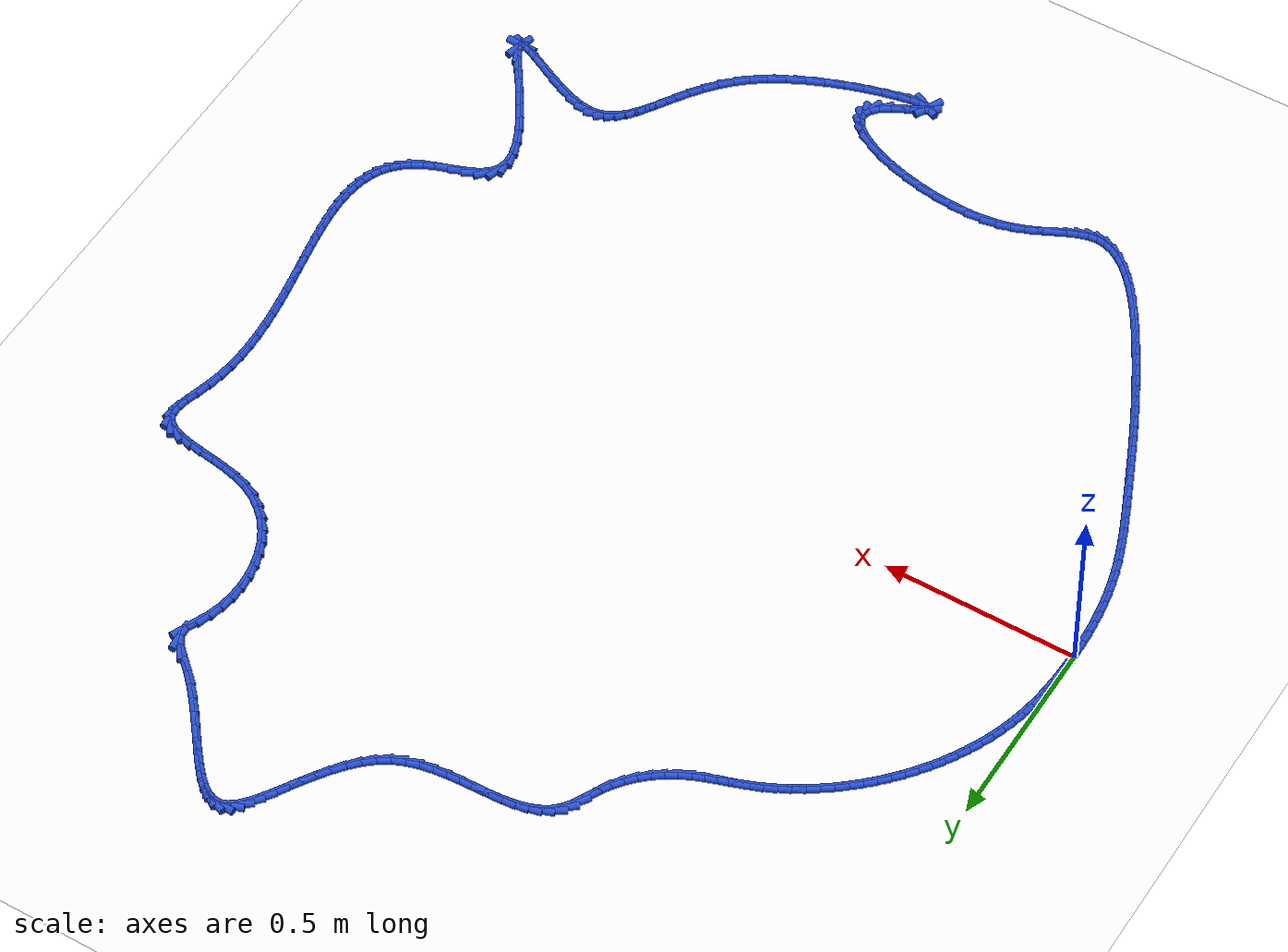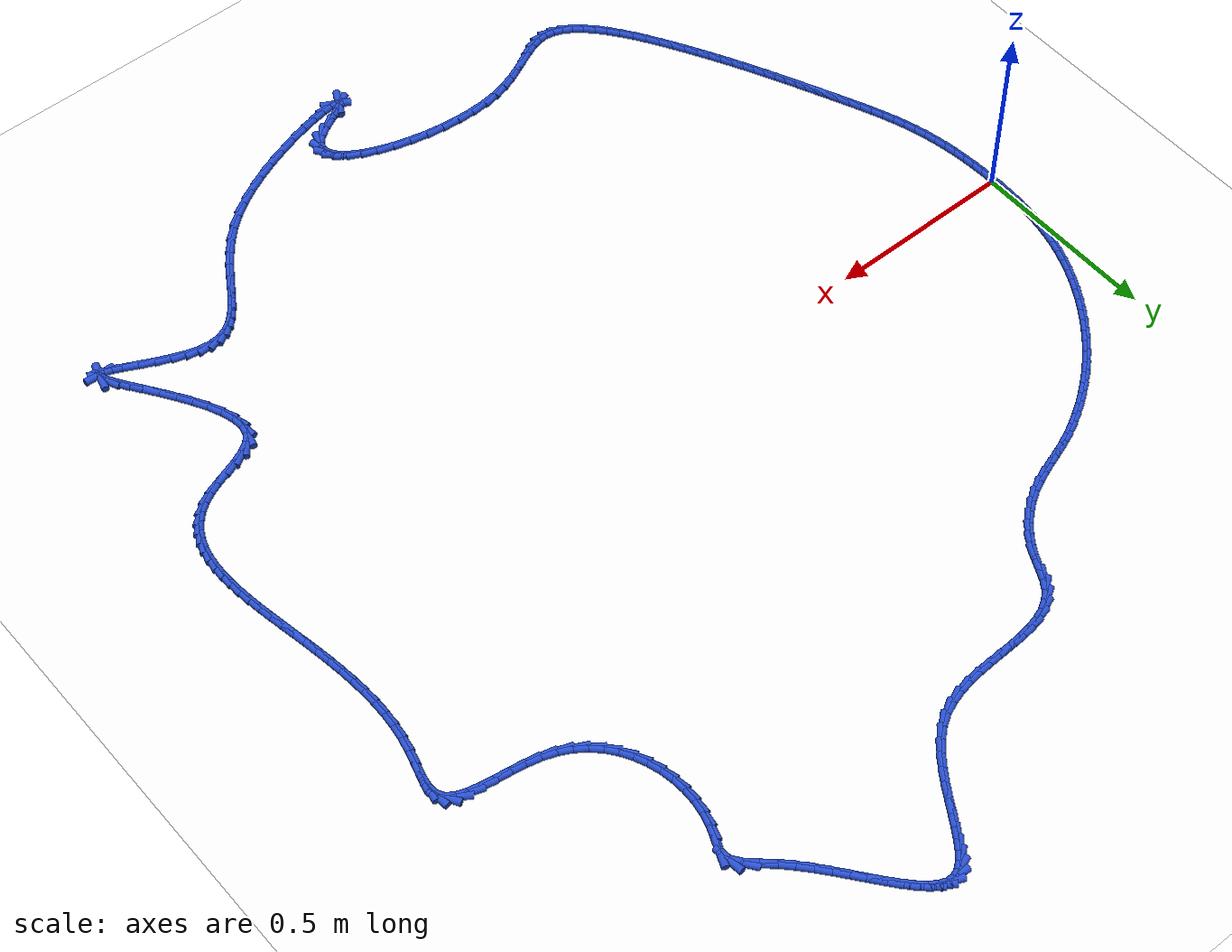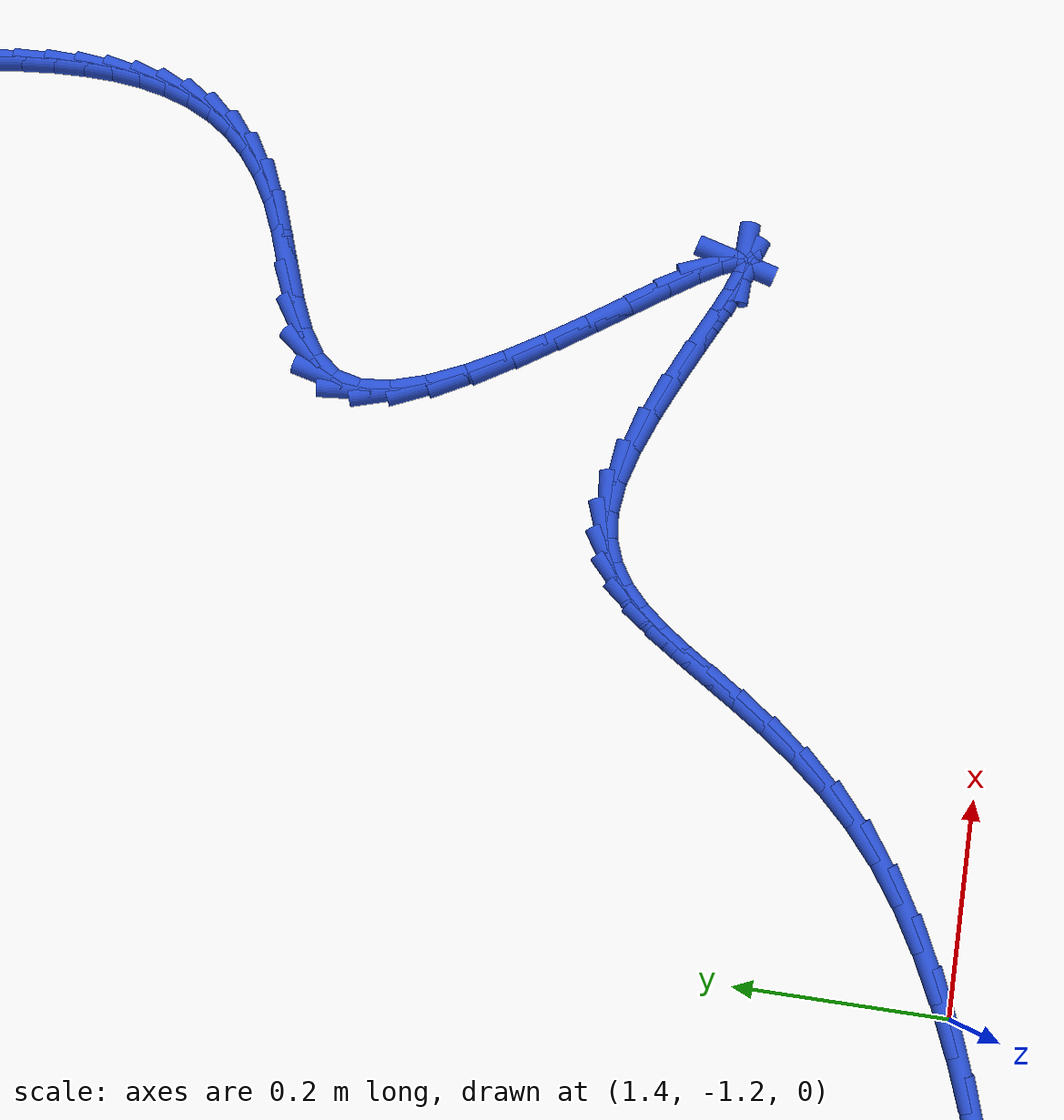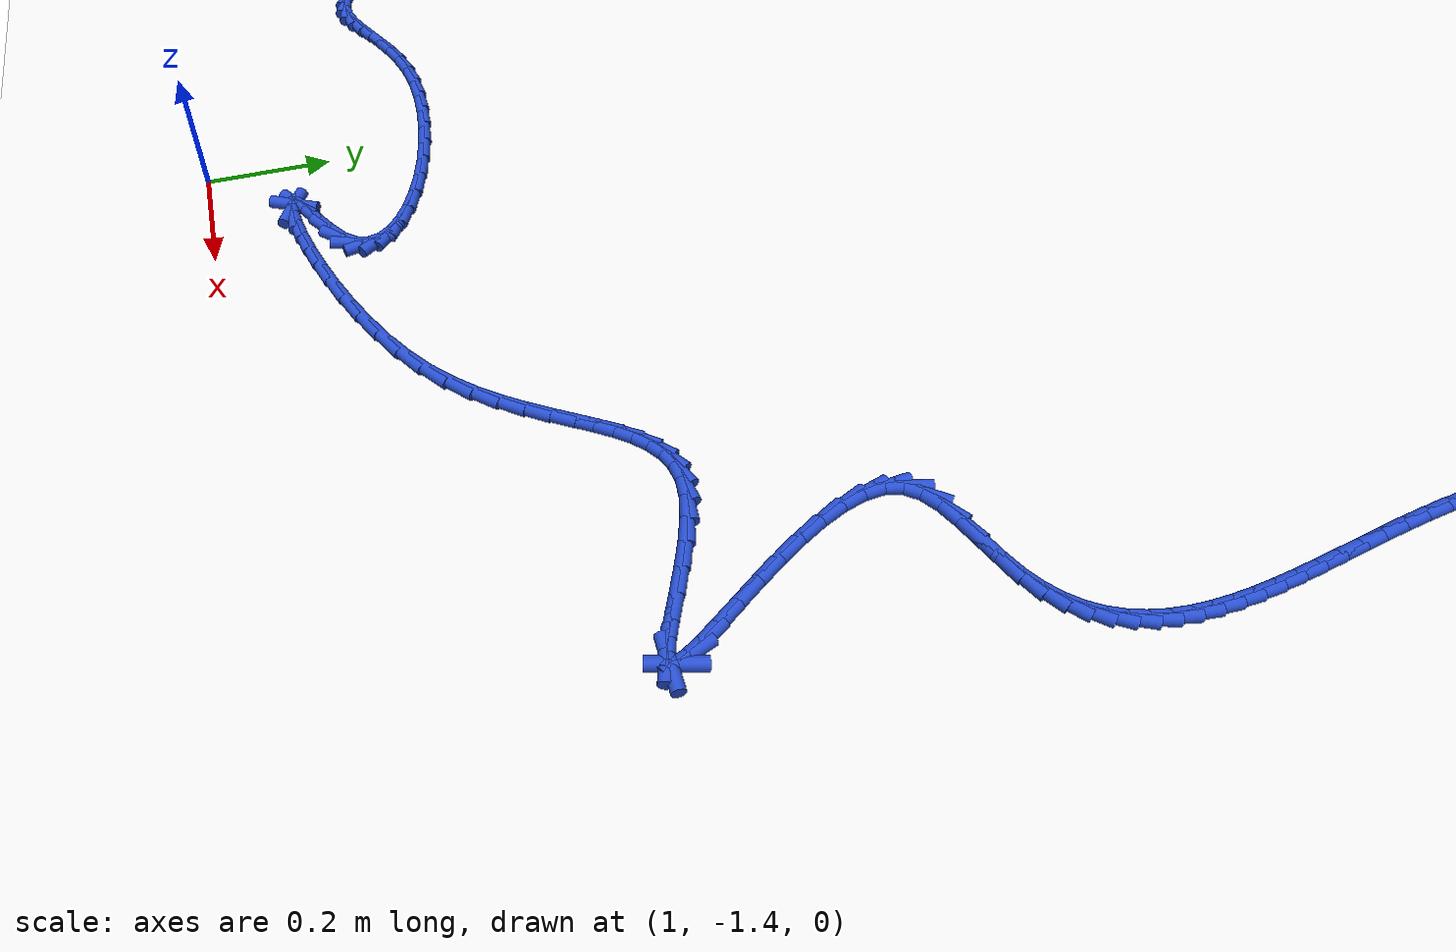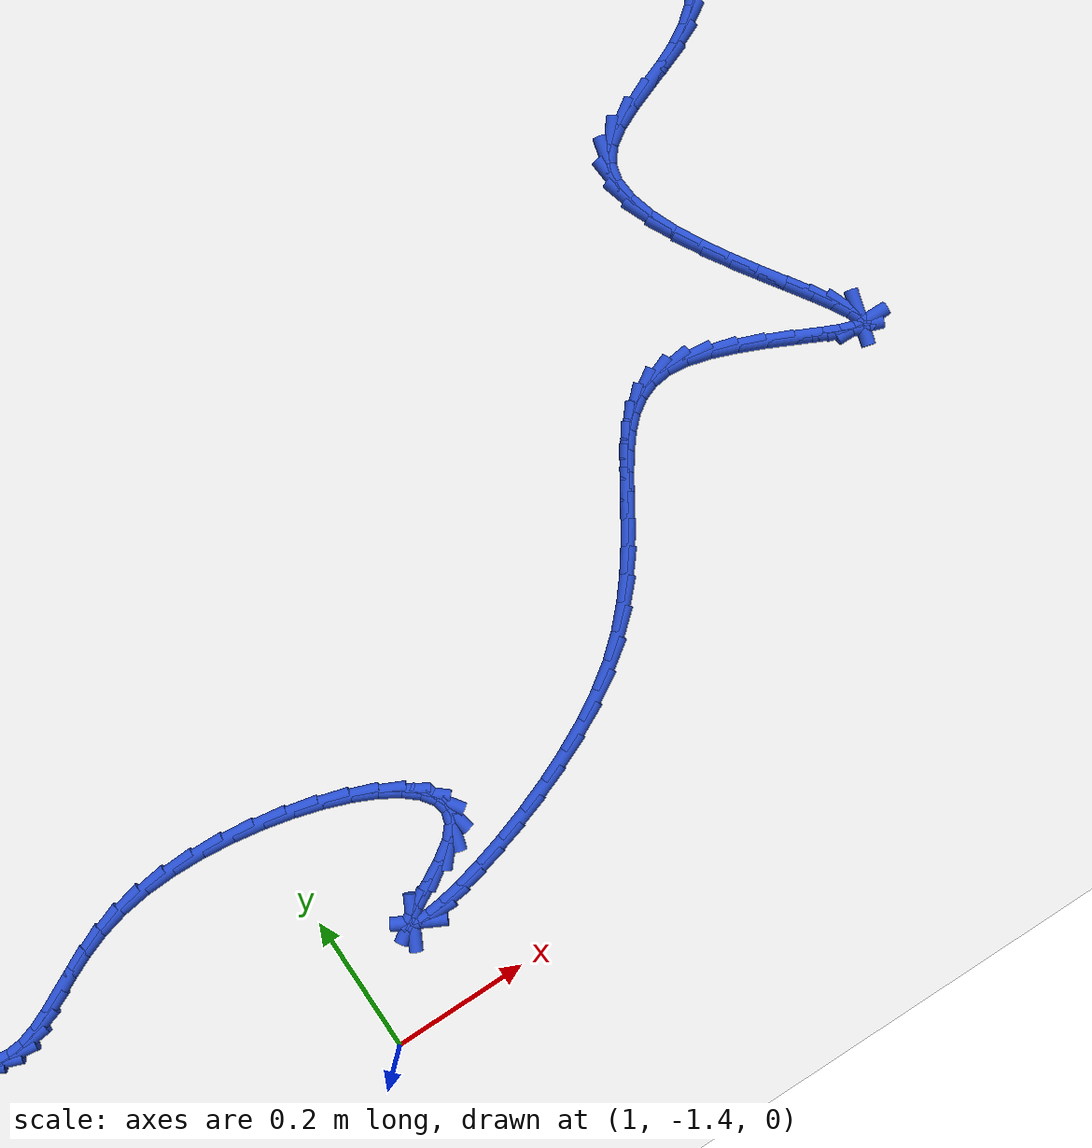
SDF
<sdf version="1.6">
 <world name="default">
  <light name="sun" type="directional">
   <pose>0 0 10 0 -0 0</pose>
   <diffuse>0.8 0.8 0.8 1</diffuse>
   <specular>0.2 0.2 0.2 1</specular>
   <attenuation>
    <range>1000</range>
    <constant>0.9</constant>
    <linear>0.01</linear>
    <quadratic>0.001</quadratic>
   </attenuation>
   <direction>-0.5 0.1 -0.9</direction>
  </light>
  <model name="ground_plane">
   <static>1</static>
   <link name="link">
    <collision name="collision">
     <geometry><plane><normal>0 0 1</normal><size>100 100</size></plane></geometry>
     <surface><friction><ode><mu>100</mu><mu2>50</mu2></ode></friction></surface>
    </collision>
    <visual name="visual">
     <cast_shadows>0</cast_shadows>
     <geometry><plane><normal>0 0 1</normal><size>100 100</size></plane></geometry>
     <material>
      <script><uri>file://media/materials/scripts/gazebo.material</uri><name>Gazebo/WhiteGlow</name></script>
     </material>
    </visual>
   </link>
  </model>
  <gravity>0 0 -9.8</gravity>
  <magnetic_field>6e-06 2.3e-05 -4.2e-05</magnetic_field>
  <atmosphere type="adiabatic"/>
  <physics name="default_physics" default="0" type="ode">
   <max_step_size>0.001</max_step_size>
   <real_time_factor>1</real_time_factor>
   <real_time_update_rate>1000</real_time_update_rate>
  </physics>
  <scene><ambient>0.4 0.4 0.4 1</ambient><background>0.7 0.7 0.7 1</background><shadows>1</shadows></scene>
  <spherical_coordinates>
   <surface_model>EARTH_WGS84</surface_model>
   <latitude_deg>0</latitude_deg>
   <longitude_deg>0</longitude_deg>
   <elevation>0</elevation>
   <heading_deg>0</heading_deg>
  </spherical_coordinates>
  <model name="line">
   <link name="link_0">
    <pose>-1.3010426069826053e-18 -2.0816681711721685e-17 0.01 0 1.57 1.5652417687050806</pose>
    <collision name="collision">
     <geometry><cylinder><radius>0.01</radius><length>0.08</length></cylinder></geometry>
    </collision>
    <visual name="visual">
     <material>
      <script><name>Gazebo/Blue</name><uri>file://media/materials/scripts/gazebo.material</uri></script>
     </material>
     <geometry><cylinder><radius>0.01</radius><length>0.08</length></cylinder></geometry>
    </visual>
   </link>
   <link name="link_1">
    <pose>0.0001733001976537485 0.031199316410812177 0.01 0 1.57 1.53811177170229</pose>
    <collision name="collision">
     <geometry><cylinder><radius>0.01</radius><length>0.08</length></cylinder></geometry>
    </collision>
    <visual name="visual">
     <material>
      <script><name>Gazebo/Blue</name><uri>file://media/materials/scripts/gazebo.material</uri></script>
     </material>
     <geometry><cylinder><radius>0.01</radius><length>0.08</length></cylinder></geometry>
    </visual>
   </link>
   <link name="link_2">
    <pose>0.0011924847750177342 0.06237066397072591 0.01 0 1.57 1.5073699337999211</pose>
    <collision name="collision">
     <geometry><cylinder><radius>0.01</radius><length>0.08</length></cylinder></geometry>
    </collision>
    <visual name="visual">
     <material>
      <script><name>Gazebo/Blue</name><uri>file://media/materials/scripts/gazebo.material</uri></script>
     </material>
     <geometry><cylinder><radius>0.01</radius><length>0.08</length></cylinder></geometry>
    </visual>
   </link>
   <link name="link_3">
    <pose>0.0031680086409162783 0.09347560223872242 0.01 0 1.57 1.4729705740794885</pose>
    <collision name="collision">
     <geometry><cylinder><radius>0.01</radius><length>0.08</length></cylinder></geometry>
    </collision>
    <visual name="visual">
     <material>
      <script><name>Gazebo/Blue</name><uri>file://media/materials/scripts/gazebo.material</uri></script>
     </material>
     <geometry><cylinder><radius>0.01</radius><length>0.08</length></cylinder></geometry>
    </visual>
   </link>
   <link name="link_4">
    <pose>0.006210326704173702 0.12447569077378302 0.01 0 1.57 1.4348925035926217</pose>
    <collision name="collision">
     <geometry><cylinder><radius>0.01</radius><length>0.08</length></cylinder></geometry>
    </collision>
    <visual name="visual">
     <material>
      <script><name>Gazebo/Blue</name><uri>file://media/materials/scripts/gazebo.material</uri></script>
     </material>
     <geometry><cylinder><radius>0.01</radius><length>0.08</length></cylinder></geometry>
    </visual>
   </link>
   <link name="link_5">
    <pose>0.01042989387361433 0.155332489134889 0.01 0 1.57 1.3931531087541023</pose>
    <collision name="collision">
     <geometry><cylinder><radius>0.01</radius><length>0.08</length></cylinder></geometry>
    </collision>
    <visual name="visual">
     <material>
      <script><name>Gazebo/Blue</name><uri>file://media/materials/scripts/gazebo.material</uri></script>
     </material>
     <geometry><cylinder><radius>0.01</radius><length>0.08</length></cylinder></geometry>
    </visual>
   </link>
   <link name="link_6">
    <pose>0.01593716505806247 0.18600755688102155 0.01 0 1.57 1.3478236340478975</pose>
    <collision name="collision">
     <geometry><cylinder><radius>0.01</radius><length>0.08</length></cylinder></geometry>
    </collision>
    <visual name="visual">
     <material>
      <script><name>Gazebo/Blue</name><uri>file://media/materials/scripts/gazebo.material</uri></script>
     </material>
     <geometry><cylinder><radius>0.01</radius><length>0.08</length></cylinder></geometry>
    </visual>
   </link>
   <link name="link_7">
    <pose>0.022842595166342457 0.21646245357116203 0.01 0 1.57 1.2990565114552943</pose>
    <collision name="collision">
     <geometry><cylinder><radius>0.01</radius><length>0.08</length></cylinder></geometry>
    </collision>
    <visual name="visual">
     <material>
      <script><name>Gazebo/Blue</name><uri>file://media/materials/scripts/gazebo.material</uri></script>
     </material>
     <geometry><cylinder><radius>0.01</radius><length>0.08</length></cylinder></geometry>
    </visual>
   </link>
   <link name="link_8">
    <pose>0.031256233099674874 0.24665867801433464 0.01 0 1.57 1.2485645808949022</pose>
    <collision name="collision">
     <geometry><cylinder><radius>0.01</radius><length>0.08</length></cylinder></geometry>
    </collision>
    <visual name="visual">
     <material>
      <script><name>Gazebo/Blue</name><uri>file://media/materials/scripts/gazebo.material</uri></script>
     </material>
     <geometry><cylinder><radius>0.01</radius><length>0.08</length></cylinder></geometry>
    </visual>
   </link>
   <link name="link_9">
    <pose>0.041235965954750826 0.27654992417217855 0.01 0 1.57 1.199347240741251</pose>
    <collision name="collision">
     <geometry><cylinder><radius>0.01</radius><length>0.08</length></cylinder></geometry>
    </collision>
    <visual name="visual">
     <material>
      <script><name>Gazebo/Blue</name><uri>file://media/materials/scripts/gazebo.material</uri></script>
     </material>
     <geometry><cylinder><radius>0.01</radius><length>0.08</length></cylinder></geometry>
    </visual>
   </link>
   <link name="link_10">
    <pose>0.0527367000599913 0.3060744772376519 0.01 0 1.57 1.1516035880465487</pose>
    <collision name="collision">
     <geometry><cylinder><radius>0.01</radius><length>0.08</length></cylinder></geometry>
    </collision>
    <visual name="visual">
     <material>
      <script><name>Gazebo/Blue</name><uri>file://media/materials/scripts/gazebo.material</uri></script>
     </material>
     <geometry><cylinder><radius>0.01</radius><length>0.08</length></cylinder></geometry>
    </visual>
   </link>
   <link name="link_11">
    <pose>0.0657012727735915 0.3351688165522568 0.01 0 1.57 1.1051662196073389</pose>
    <collision name="collision">
     <geometry><cylinder><radius>0.01</radius><length>0.08</length></cylinder></geometry>
    </collision>
    <visual name="visual">
     <material>
      <script><name>Gazebo/Blue</name><uri>file://media/materials/scripts/gazebo.material</uri></script>
     </material>
     <geometry><cylinder><radius>0.01</radius><length>0.08</length></cylinder></geometry>
    </visual>
   </link>
   <link name="link_12">
    <pose>0.08007252145374649 0.3637694214574944 0.01 0 1.57 1.0598605843184021</pose>
    <collision name="collision">
     <geometry><cylinder><radius>0.01</radius><length>0.08</length></cylinder></geometry>
    </collision>
    <visual name="visual">
     <material>
      <script><name>Gazebo/Blue</name><uri>file://media/materials/scripts/gazebo.material</uri></script>
     </material>
     <geometry><cylinder><radius>0.01</radius><length>0.08</length></cylinder></geometry>
    </visual>
   </link>
   <link name="link_13">
    <pose>0.09579328345865135 0.39181277129486636 0.01 0 1.57 1.0155078279892866</pose>
    <collision name="collision">
     <geometry><cylinder><radius>0.01</radius><length>0.08</length></cylinder></geometry>
    </collision>
    <visual name="visual">
     <material>
      <script><name>Gazebo/Blue</name><uri>file://media/materials/scripts/gazebo.material</uri></script>
     </material>
     <geometry><cylinder><radius>0.01</radius><length>0.08</length></cylinder></geometry>
    </visual>
   </link>
   <link name="link_14">
    <pose>0.11280639614650119 0.41923534540587415 0.01 0 1.57 0.9719267776762458</pose>
    <collision name="collision">
     <geometry><cylinder><radius>0.01</radius><length>0.08</length></cylinder></geometry>
    </collision>
    <visual name="visual">
     <material>
      <script><name>Gazebo/Blue</name><uri>file://media/materials/scripts/gazebo.material</uri></script>
     </material>
     <geometry><cylinder><radius>0.01</radius><length>0.08</length></cylinder></geometry>
    </visual>
   </link>
   <link name="link_15">
    <pose>0.13105469687549107 0.4459736231320193 0.01 0 1.57 0.9289352324854522</pose>
    <collision name="collision">
     <geometry><cylinder><radius>0.01</radius><length>0.08</length></cylinder></geometry>
    </collision>
    <visual name="visual">
     <material>
      <script><name>Gazebo/Blue</name><uri>file://media/materials/scripts/gazebo.material</uri></script>
     </material>
     <geometry><cylinder><radius>0.01</radius><length>0.08</length></cylinder></geometry>
    </visual>
   </link>
   <link name="link_16">
    <pose>0.1504810230038161 0.4719640838148034 0.01 0 1.57 0.8863507195687078</pose>
    <collision name="collision">
     <geometry><cylinder><radius>0.01</radius><length>0.08</length></cylinder></geometry>
    </collision>
    <visual name="visual">
     <material>
      <script><name>Gazebo/Blue</name><uri>file://media/materials/scripts/gazebo.material</uri></script>
     </material>
     <geometry><cylinder><radius>0.01</radius><length>0.08</length></cylinder></geometry>
    </visual>
   </link>
   <link name="link_17">
    <pose>0.17102821188967152 0.4971432067957281 0.01 0 1.57 0.843990860754449</pose>
    <collision name="collision">
     <geometry><cylinder><radius>0.01</radius><length>0.08</length></cylinder></geometry>
    </collision>
    <visual name="visual">
     <material>
      <script><name>Gazebo/Blue</name><uri>file://media/materials/scripts/gazebo.material</uri></script>
     </material>
     <geometry><cylinder><radius>0.01</radius><length>0.08</length></cylinder></geometry>
    </visual>
   </link>
   <link name="link_18">
    <pose>0.1926391008912522 0.5214474714162946 0.01 0 1.57 0.8016734816768494</pose>
    <collision name="collision">
     <geometry><cylinder><radius>0.01</radius><length>0.08</length></cylinder></geometry>
    </collision>
    <visual name="visual">
     <material>
      <script><name>Gazebo/Blue</name><uri>file://media/materials/scripts/gazebo.material</uri></script>
     </material>
     <geometry><cylinder><radius>0.01</radius><length>0.08</length></cylinder></geometry>
    </visual>
   </link>
   <link name="link_19">
    <pose>0.21525652736675335 0.5448133570180047 0.01 0 1.57 0.7592165843336431</pose>
    <collision name="collision">
     <geometry><cylinder><radius>0.01</radius><length>0.08</length></cylinder></geometry>
    </collision>
    <visual name="visual">
     <material>
      <script><name>Gazebo/Blue</name><uri>file://media/materials/scripts/gazebo.material</uri></script>
     </material>
     <geometry><cylinder><radius>0.01</radius><length>0.08</length></cylinder></geometry>
    </visual>
   </link>
   <link name="link_20">
    <pose>0.23882332867437006 0.5671773429423599 0.01 0 1.57 0.7164382973901072</pose>
    <collision name="collision">
     <geometry><cylinder><radius>0.01</radius><length>0.08</length></cylinder></geometry>
    </collision>
    <visual name="visual">
     <material>
      <script><name>Gazebo/Blue</name><uri>file://media/materials/scripts/gazebo.material</uri></script>
     </material>
     <geometry><cylinder><radius>0.01</radius><length>0.08</length></cylinder></geometry>
    </visual>
   </link>
   <link name="link_21">
    <pose>0.26328234217229746 0.5884759085308615 0.01 0 1.57 0.673156917025306</pose>
    <collision name="collision">
     <geometry><cylinder><radius>0.01</radius><length>0.08</length></cylinder></geometry>
    </collision>
    <visual name="visual">
     <material>
      <script><name>Gazebo/Blue</name><uri>file://media/materials/scripts/gazebo.material</uri></script>
     </material>
     <geometry><cylinder><radius>0.01</radius><length>0.08</length></cylinder></geometry>
    </visual>
   </link>
   <link name="link_22">
    <pose>0.2885764052187306 0.6086455331250114 0.01 0 1.57 0.629191154778254</pose>
    <collision name="collision">
     <geometry><cylinder><radius>0.01</radius><length>0.08</length></cylinder></geometry>
    </collision>
    <visual name="visual">
     <material>
      <script><name>Gazebo/Blue</name><uri>file://media/materials/scripts/gazebo.material</uri></script>
     </material>
     <geometry><cylinder><radius>0.01</radius><length>0.08</length></cylinder></geometry>
    </visual>
   </link>
   <link name="link_23">
    <pose>0.3146483551718646 0.6276226960663109 0.01 0 1.57 0.5843607171446917</pose>
    <collision name="collision">
     <geometry><cylinder><radius>0.01</radius><length>0.08</length></cylinder></geometry>
    </collision>
    <visual name="visual">
     <material>
      <script><name>Gazebo/Blue</name><uri>file://media/materials/scripts/gazebo.material</uri></script>
     </material>
     <geometry><cylinder><radius>0.01</radius><length>0.08</length></cylinder></geometry>
    </visual>
   </link>
   <link name="link_24">
    <pose>0.34144102938989457 0.6453438766962616 0.01 0 1.57 0.5384873532756794</pose>
    <collision name="collision">
     <geometry><cylinder><radius>0.01</radius><length>0.08</length></cylinder></geometry>
    </collision>
    <visual name="visual">
     <material>
      <script><name>Gazebo/Blue</name><uri>file://media/materials/scripts/gazebo.material</uri></script>
     </material>
     <geometry><cylinder><radius>0.01</radius><length>0.08</length></cylinder></geometry>
    </visual>
   </link>
   <link name="link_25">
    <pose>0.3688972652310155 0.6617455543563648 0.01 0 1.57 0.49139651964454045</pose>
    <collision name="collision">
     <geometry><cylinder><radius>0.01</radius><length>0.08</length></cylinder></geometry>
    </collision>
    <visual name="visual">
     <material>
      <script><name>Gazebo/Blue</name><uri>file://media/materials/scripts/gazebo.material</uri></script>
     </material>
     <geometry><cylinder><radius>0.01</radius><length>0.08</length></cylinder></geometry>
    </visual>
   </link>
   <link name="link_26">
    <pose>0.39695990005342263 0.6767642083881223 0.01 0 1.57 0.4429198200799857</pose>
    <collision name="collision">
     <geometry><cylinder><radius>0.01</radius><length>0.08</length></cylinder></geometry>
    </collision>
    <visual name="visual">
     <material>
      <script><name>Gazebo/Blue</name><uri>file://media/materials/scripts/gazebo.material</uri></script>
     </material>
     <geometry><cylinder><radius>0.01</radius><length>0.08</length></cylinder></geometry>
    </visual>
   </link>
   <link name="link_27">
    <pose>0.4255717712153111 0.6903363181330358 0.01 0 1.57 0.3929024159851765</pose>
    <collision name="collision">
     <geometry><cylinder><radius>0.01</radius><length>0.08</length></cylinder></geometry>
    </collision>
    <visual name="visual">
     <material>
      <script><name>Gazebo/Blue</name><uri>file://media/materials/scripts/gazebo.material</uri></script>
     </material>
     <geometry><cylinder><radius>0.01</radius><length>0.08</length></cylinder></geometry>
    </visual>
   </link>
   <link name="link_28">
    <pose>0.4546756800937663 0.7023984856530187 0.01 0 1.57 0.3479335227404338</pose>
    <collision name="collision">
     <geometry><cylinder><radius>0.01</radius><length>0.08</length></cylinder></geometry>
    </collision>
    <visual name="visual">
     <material>
      <script><name>Gazebo/Blue</name><uri>file://media/materials/scripts/gazebo.material</uri></script>
     </material>
     <geometry><cylinder><radius>0.01</radius><length>0.08</length></cylinder></geometry>
    </visual>
   </link>
   <link name="link_29">
    <pose>0.4841549230970011 0.713090266015008 0.01 0 1.57 0.3285991722100279</pose>
    <collision name="collision">
     <geometry><cylinder><radius>0.01</radius><length>0.08</length></cylinder></geometry>
    </collision>
    <visual name="visual">
     <material>
      <script><name>Gazebo/Blue</name><uri>file://media/materials/scripts/gazebo.material</uri></script>
     </material>
     <geometry><cylinder><radius>0.01</radius><length>0.08</length></cylinder></geometry>
    </visual>
   </link>
   <link name="link_30">
    <pose>0.5137119455207557 0.7231680413750641 0.01 0 1.57 0.33913069611313496</pose>
    <collision name="collision">
     <geometry><cylinder><radius>0.01</radius><length>0.08</length></cylinder></geometry>
    </collision>
    <visual name="visual">
     <material>
      <script><name>Gazebo/Blue</name><uri>file://media/materials/scripts/gazebo.material</uri></script>
     </material>
     <geometry><cylinder><radius>0.01</radius><length>0.08</length></cylinder></geometry>
    </visual>
   </link>
   <link name="link_31">
    <pose>0.5430149612038004 0.733504946778795 0.01 0 1.57 0.37997436462901174</pose>
    <collision name="collision">
     <geometry><cylinder><radius>0.01</radius><length>0.08</length></cylinder></geometry>
    </collision>
    <visual name="visual">
     <material>
      <script><name>Gazebo/Blue</name><uri>file://media/materials/scripts/gazebo.material</uri></script>
     </material>
     <geometry><cylinder><radius>0.01</radius><length>0.08</length></cylinder></geometry>
    </visual>
   </link>
   <link name="link_32">
    <pose>0.5717321839849059 0.7449741172718083 0.01 0 1.57 0.4513140826915281</pose>
    <collision name="collision">
     <geometry><cylinder><radius>0.01</radius><length>0.08</length></cylinder></geometry>
    </collision>
    <visual name="visual">
     <material>
      <script><name>Gazebo/Blue</name><uri>file://media/materials/scripts/gazebo.material</uri></script>
     </material>
     <geometry><cylinder><radius>0.01</radius><length>0.08</length></cylinder></geometry>
    </visual>
   </link>
   <link name="link_33">
    <pose>0.5995318759896858 0.7584479833012294 0.01 0 1.57 0.5445255486009554</pose>
    <collision name="collision">
     <geometry><cylinder><radius>0.01</radius><length>0.08</length></cylinder></geometry>
    </collision>
    <visual name="visual">
     <material>
      <script><name>Gazebo/Blue</name><uri>file://media/materials/scripts/gazebo.material</uri></script>
     </material>
     <geometry><cylinder><radius>0.01</radius><length>0.08</length></cylinder></geometry>
    </visual>
   </link>
   <link name="link_34">
    <pose>0.6261002040547045 0.774537710934754 0.01 0 1.57 0.6400494288537218</pose>
    <collision name="collision">
     <geometry><cylinder><radius>0.01</radius><length>0.08</length></cylinder></geometry>
    </collision>
    <visual name="visual">
     <material>
      <script><name>Gazebo/Blue</name><uri>file://media/materials/scripts/gazebo.material</uri></script>
     </material>
     <geometry><cylinder><radius>0.01</radius><length>0.08</length></cylinder></geometry>
    </visual>
   </link>
   <link name="link_35">
    <pose>0.6511679353271846 0.7932036614033307 0.01 0 1.57 0.7358562967704068</pose>
    <collision name="collision">
     <geometry><cylinder><radius>0.01</radius><length>0.08</length></cylinder></geometry>
    </collision>
    <visual name="visual">
     <material>
      <script><name>Gazebo/Blue</name><uri>file://media/materials/scripts/gazebo.material</uri></script>
     </material>
     <geometry><cylinder><radius>0.01</radius><length>0.08</length></cylinder></geometry>
    </visual>
   </link>
   <link name="link_36">
    <pose>0.6744726655549093 0.8143065534420006 0.01 0 1.57 0.8328386658747416</pose>
    <collision name="collision">
     <geometry><cylinder><radius>0.01</radius><length>0.08</length></cylinder></geometry>
    </collision>
    <visual name="visual">
     <material>
      <script><name>Gazebo/Blue</name><uri>file://media/materials/scripts/gazebo.material</uri></script>
     </material>
     <geometry><cylinder><radius>0.01</radius><length>0.08</length></cylinder></geometry>
    </visual>
   </link>
   <link name="link_37">
    <pose>0.6957519904856617 0.8377071057858058 0.01 0 1.57 0.9317593012357724</pose>
    <collision name="collision">
     <geometry><cylinder><radius>0.01</radius><length>0.08</length></cylinder></geometry>
    </collision>
    <visual name="visual">
     <material>
      <script><name>Gazebo/Blue</name><uri>file://media/materials/scripts/gazebo.material</uri></script>
     </material>
     <geometry><cylinder><radius>0.01</radius><length>0.08</length></cylinder></geometry>
    </visual>
   </link>
   <link name="link_38">
    <pose>0.7147435058672249 0.863266037169787 0.01 0 1.57 1.0331886598580435</pose>
    <collision name="collision">
     <geometry><cylinder><radius>0.01</radius><length>0.08</length></cylinder></geometry>
    </collision>
    <visual name="visual">
     <material>
      <script><name>Gazebo/Blue</name><uri>file://media/materials/scripts/gazebo.material</uri></script>
     </material>
     <geometry><cylinder><radius>0.01</radius><length>0.08</length></cylinder></geometry>
    </visual>
   </link>
   <link name="link_39">
    <pose>0.7311849538564488 0.8908439222533747 0.01 0 1.57 1.1142629824593673</pose>
    <collision name="collision">
     <geometry><cylinder><radius>0.01</radius><length>0.08</length></cylinder></geometry>
    </collision>
    <visual name="visual">
     <material>
      <script><name>Gazebo/Blue</name><uri>file://media/materials/scripts/gazebo.material</uri></script>
     </material>
     <geometry><cylinder><radius>0.01</radius><length>0.08</length></cylinder></geometry>
    </visual>
   </link>
   <link name="link_40">
    <pose>0.7453793986582609 0.9197450237053043 0.01 0 1.57 1.100254172061006</pose>
    <collision name="collision">
     <geometry><cylinder><radius>0.01</radius><length>0.08</length></cylinder></geometry>
    </collision>
    <visual name="visual">
     <material>
      <script><name>Gazebo/Blue</name><uri>file://media/materials/scripts/gazebo.material</uri></script>
     </material>
     <geometry><cylinder><radius>0.01</radius><length>0.08</length></cylinder></geometry>
    </visual>
   </link>
   <link name="link_41">
    <pose>0.7594753394588776 0.9474575816074924 0.01 0 1.57 0.9621424991500096</pose>
    <collision name="collision">
     <geometry><cylinder><radius>0.01</radius><length>0.08</length></cylinder></geometry>
    </collision>
    <visual name="visual">
     <material>
      <script><name>Gazebo/Blue</name><uri>file://media/materials/scripts/gazebo.material</uri></script>
     </material>
     <geometry><cylinder><radius>0.01</radius><length>0.08</length></cylinder></geometry>
    </visual>
   </link>
   <link name="link_42">
    <pose>0.7759729331753005 0.9711298325374123 0.01 0 1.57 0.733224505251834</pose>
    <collision name="collision">
     <geometry><cylinder><radius>0.01</radius><length>0.08</length></cylinder></geometry>
    </collision>
    <visual name="visual">
     <material>
      <script><name>Gazebo/Blue</name><uri>file://media/materials/scripts/gazebo.material</uri></script>
     </material>
     <geometry><cylinder><radius>0.01</radius><length>0.08</length></cylinder></geometry>
    </visual>
   </link>
   <link name="link_43">
    <pose>0.7962030015291083 0.9893518904730628 0.01 0 1.57 0.5162934782600339</pose>
    <collision name="collision">
     <geometry><cylinder><radius>0.01</radius><length>0.08</length></cylinder></geometry>
    </collision>
    <visual name="visual">
     <material>
      <script><name>Gazebo/Blue</name><uri>file://media/materials/scripts/gazebo.material</uri></script>
     </material>
     <geometry><cylinder><radius>0.01</radius><length>0.08</length></cylinder></geometry>
    </visual>
   </link>
   <link name="link_44">
    <pose>0.8198326947566742 1.0027653002617185 0.01 0 1.57 0.34014566376443633</pose>
    <collision name="collision">
     <geometry><cylinder><radius>0.01</radius><length>0.08</length></cylinder></geometry>
    </collision>
    <visual name="visual">
     <material>
      <script><name>Gazebo/Blue</name><uri>file://media/materials/scripts/gazebo.material</uri></script>
     </material>
     <geometry><cylinder><radius>0.01</radius><length>0.08</length></cylinder></geometry>
    </visual>
   </link>
   <link name="link_45">
    <pose>0.8464021325058383 1.0121682449289093 0.01 0 1.57 0.20996784043331987</pose>
    <collision name="collision">
     <geometry><cylinder><radius>0.01</radius><length>0.08</length></cylinder></geometry>
    </collision>
    <visual name="visual">
     <material>
      <script><name>Gazebo/Blue</name><uri>file://media/materials/scripts/gazebo.material</uri></script>
     </material>
     <geometry><cylinder><radius>0.01</radius><length>0.08</length></cylinder></geometry>
    </visual>
   </link>
   <link name="link_46">
    <pose>0.875451434424441 1.0183589075001658 0.01 0 1.57 0.12095955384446175</pose>
    <collision name="collision">
     <geometry><cylinder><radius>0.01</radius><length>0.08</length></cylinder></geometry>
    </collision>
    <visual name="visual">
     <material>
      <script><name>Gazebo/Blue</name><uri>file://media/materials/scripts/gazebo.material</uri></script>
     </material>
     <geometry><cylinder><radius>0.01</radius><length>0.08</length></cylinder></geometry>
    </visual>
   </link>
   <link name="link_47">
    <pose>0.9065207201603223 1.0221354710010182 0.01 0 1.57 0.0661213031515337</pose>
    <collision name="collision">
     <geometry><cylinder><radius>0.01</radius><length>0.08</length></cylinder></geometry>
    </collision>
    <visual name="visual">
     <material>
      <script><name>Gazebo/Blue</name><uri>file://media/materials/scripts/gazebo.material</uri></script>
     </material>
     <geometry><cylinder><radius>0.01</radius><length>0.08</length></cylinder></geometry>
    </visual>
   </link>
   <link name="link_48">
    <pose>0.939150109361322 1.0242961184569968 0.01 0 1.57 0.039793090971080046</pose>
    <collision name="collision">
     <geometry><cylinder><radius>0.01</radius><length>0.08</length></cylinder></geometry>
    </collision>
    <visual name="visual">
     <material>
      <script><name>Gazebo/Blue</name><uri>file://media/materials/scripts/gazebo.material</uri></script>
     </material>
     <geometry><cylinder><radius>0.01</radius><length>0.08</length></cylinder></geometry>
    </visual>
   </link>
   <link name="link_49">
    <pose>0.9728797216752806 1.025639032893632 0.01 0 1.57 0.038484515006668364</pose>
    <collision name="collision">
     <geometry><cylinder><radius>0.01</radius><length>0.08</length></cylinder></geometry>
    </collision>
    <visual name="visual">
     <material>
      <script><name>Gazebo/Blue</name><uri>file://media/materials/scripts/gazebo.material</uri></script>
     </material>
     <geometry><cylinder><radius>0.01</radius><length>0.08</length></cylinder></geometry>
    </visual>
   </link>
   <link name="link_50">
    <pose>1.0072496767500383 1.026962397336454 0.01 0 1.57 0.060763660077093266</pose>
    <collision name="collision">
     <geometry><cylinder><radius>0.01</radius><length>0.08</length></cylinder></geometry>
    </collision>
    <visual name="visual">
     <material>
      <script><name>Gazebo/Blue</name><uri>file://media/materials/scripts/gazebo.material</uri></script>
     </material>
     <geometry><cylinder><radius>0.01</radius><length>0.08</length></cylinder></geometry>
    </visual>
   </link>
   <link name="link_51">
    <pose>1.041800094233435 1.029064394810993 0.01 0 1.57 0.10693531760168003</pose>
    <collision name="collision">
     <geometry><cylinder><radius>0.01</radius><length>0.08</length></cylinder></geometry>
    </collision>
    <visual name="visual">
     <material>
      <script><name>Gazebo/Blue</name><uri>file://media/materials/scripts/gazebo.material</uri></script>
     </material>
     <geometry><cylinder><radius>0.01</radius><length>0.08</length></cylinder></geometry>
    </visual>
   </link>
   <link name="link_52">
    <pose>1.0760710937733098 1.032743208342779 0.01 0 1.57 0.1786159209958354</pose>
    <collision name="collision">
     <geometry><cylinder><radius>0.01</radius><length>0.08</length></cylinder></geometry>
    </collision>
    <visual name="visual">
     <material>
      <script><name>Gazebo/Blue</name><uri>file://media/materials/scripts/gazebo.material</uri></script>
     </material>
     <geometry><cylinder><radius>0.01</radius><length>0.08</length></cylinder></geometry>
    </visual>
   </link>
   <link name="link_53">
    <pose>1.1096027950175047 1.038797020957343 0.01 0 1.57 0.27798884268821783</pose>
    <collision name="collision">
     <geometry><cylinder><radius>0.01</radius><length>0.08</length></cylinder></geometry>
    </collision>
    <visual name="visual">
     <material>
      <script><name>Gazebo/Blue</name><uri>file://media/materials/scripts/gazebo.material</uri></script>
     </material>
     <geometry><cylinder><radius>0.01</radius><length>0.08</length></cylinder></geometry>
    </visual>
   </link>
   <link name="link_54">
    <pose>1.1419353176138585 1.0480240156802145 0.01 0 1.57 0.4063393460674552</pose>
    <collision name="collision">
     <geometry><cylinder><radius>0.01</radius><length>0.08</length></cylinder></geometry>
    </collision>
    <visual name="visual">
     <material>
      <script><name>Gazebo/Blue</name><uri>file://media/materials/scripts/gazebo.material</uri></script>
     </material>
     <geometry><cylinder><radius>0.01</radius><length>0.08</length></cylinder></geometry>
    </visual>
   </link>
   <link name="link_55">
    <pose>1.172608781210212 1.0612223755369248 0.01 0 1.57 0.560175437924606</pose>
    <collision name="collision">
     <geometry><cylinder><radius>0.01</radius><length>0.08</length></cylinder></geometry>
    </collision>
    <visual name="visual">
     <material>
      <script><name>Gazebo/Blue</name><uri>file://media/materials/scripts/gazebo.material</uri></script>
     </material>
     <geometry><cylinder><radius>0.01</radius><length>0.08</length></cylinder></geometry>
    </visual>
   </link>
   <link name="link_56">
    <pose>1.201181350799106 1.0791429185618482 0.01 0 1.57 0.7058190704599503</pose>
    <collision name="collision">
     <geometry><cylinder><radius>0.01</radius><length>0.08</length></cylinder></geometry>
    </collision>
    <visual name="visual">
     <material>
      <script><name>Gazebo/Blue</name><uri>file://media/materials/scripts/gazebo.material</uri></script>
     </material>
     <geometry><cylinder><radius>0.01</radius><length>0.08</length></cylinder></geometry>
    </visual>
   </link>
   <link name="link_57">
    <pose>1.2275588137413713 1.101624031873132 0.01 0 1.57 0.8181723876559537</pose>
    <collision name="collision">
     <geometry><cylinder><radius>0.01</radius><length>0.08</length></cylinder></geometry>
    </collision>
    <visual name="visual">
     <material>
      <script><name>Gazebo/Blue</name><uri>file://media/materials/scripts/gazebo.material</uri></script>
     </material>
     <geometry><cylinder><radius>0.01</radius><length>0.08</length></cylinder></geometry>
    </visual>
   </link>
   <link name="link_58">
    <pose>1.251960798367414 1.1276803402837894 0.01 0 1.57 0.9011009147359261</pose>
    <collision name="collision">
     <geometry><cylinder><radius>0.01</radius><length>0.08</length></cylinder></geometry>
    </collision>
    <visual name="visual">
     <material>
      <script><name>Gazebo/Blue</name><uri>file://media/materials/scripts/gazebo.material</uri></script>
     </material>
     <geometry><cylinder><radius>0.01</radius><length>0.08</length></cylinder></geometry>
    </visual>
   </link>
   <link name="link_59">
    <pose>1.274618199930036 1.1562968954571624 0.01 0 1.57 0.9593938817962042</pose>
    <collision name="collision">
     <geometry><cylinder><radius>0.01</radius><length>0.08</length></cylinder></geometry>
    </collision>
    <visual name="visual">
     <material>
      <script><name>Gazebo/Blue</name><uri>file://media/materials/scripts/gazebo.material</uri></script>
     </material>
     <geometry><cylinder><radius>0.01</radius><length>0.08</length></cylinder></geometry>
    </visual>
   </link>
   <link name="link_60">
    <pose>1.2957619136820395 1.1864587490565932 0.01 0 1.57 0.996462560337881</pose>
    <collision name="collision">
     <geometry><cylinder><radius>0.01</radius><length>0.08</length></cylinder></geometry>
    </collision>
    <visual name="visual">
     <material>
      <script><name>Gazebo/Blue</name><uri>file://media/materials/scripts/gazebo.material</uri></script>
     </material>
     <geometry><cylinder><radius>0.01</radius><length>0.08</length></cylinder></geometry>
    </visual>
   </link>
   <link name="link_61">
    <pose>1.3156228348762282 1.217150952745425 0.01 0 1.57 1.0138825208584834</pose>
    <collision name="collision">
     <geometry><cylinder><radius>0.01</radius><length>0.08</length></cylinder></geometry>
    </collision>
    <visual name="visual">
     <material>
      <script><name>Gazebo/Blue</name><uri>file://media/materials/scripts/gazebo.material</uri></script>
     </material>
     <geometry><cylinder><radius>0.01</radius><length>0.08</length></cylinder></geometry>
    </visual>
   </link>
   <link name="link_62">
    <pose>1.3344318587654038 1.2473585581870004 0.01 0 1.57 1.0110584787990842</pose>
    <collision name="collision">
     <geometry><cylinder><radius>0.01</radius><length>0.08</length></cylinder></geometry>
    </collision>
    <visual name="visual">
     <material>
      <script><name>Gazebo/Blue</name><uri>file://media/materials/scripts/gazebo.material</uri></script>
     </material>
     <geometry><cylinder><radius>0.01</radius><length>0.08</length></cylinder></geometry>
    </visual>
   </link>
   <link name="link_63">
    <pose>1.3524198806023695 1.2760666170446617 0.01 0 1.57 0.9844993900886725</pose>
    <collision name="collision">
     <geometry><cylinder><radius>0.01</radius><length>0.08</length></cylinder></geometry>
    </collision>
    <visual name="visual">
     <material>
      <script><name>Gazebo/Blue</name><uri>file://media/materials/scripts/gazebo.material</uri></script>
     </material>
     <geometry><cylinder><radius>0.01</radius><length>0.08</length></cylinder></geometry>
    </visual>
   </link>
   <link name="link_64">
    <pose>1.3698177956399276 1.3022601809817511 0.01 0 1.57 0.9261493558185699</pose>
    <collision name="collision">
     <geometry><cylinder><radius>0.01</radius><length>0.08</length></cylinder></geometry>
    </collision>
    <visual name="visual">
     <material>
      <script><name>Gazebo/Blue</name><uri>file://media/materials/scripts/gazebo.material</uri></script>
     </material>
     <geometry><cylinder><radius>0.01</radius><length>0.08</length></cylinder></geometry>
    </visual>
   </link>
   <link name="link_65">
    <pose>1.3868564991308805 1.3249243016616115 0.01 0 1.57 0.8199073776465102</pose>
    <collision name="collision">
     <geometry><cylinder><radius>0.01</radius><length>0.08</length></cylinder></geometry>
    </collision>
    <visual name="visual">
     <material>
      <script><name>Gazebo/Blue</name><uri>file://media/materials/scripts/gazebo.material</uri></script>
     </material>
     <geometry><cylinder><radius>0.01</radius><length>0.08</length></cylinder></geometry>
    </visual>
   </link>
   <link name="link_66">
    <pose>1.4037668863280315 1.3430440307475857 0.01 0 1.57 0.635960166127817</pose>
    <collision name="collision">
     <geometry><cylinder><radius>0.01</radius><length>0.08</length></cylinder></geometry>
    </collision>
    <visual name="visual">
     <material>
      <script><name>Gazebo/Blue</name><uri>file://media/materials/scripts/gazebo.material</uri></script>
     </material>
     <geometry><cylinder><radius>0.01</radius><length>0.08</length></cylinder></geometry>
    </visual>
   </link>
   <link name="link_67">
    <pose>1.4207798524841826 1.355604419903016 0.01 0 1.57 0.3324213625353398</pose>
    <collision name="collision">
     <geometry><cylinder><radius>0.01</radius><length>0.08</length></cylinder></geometry>
    </collision>
    <visual name="visual">
     <material>
      <script><name>Gazebo/Blue</name><uri>file://media/materials/scripts/gazebo.material</uri></script>
     </material>
     <geometry><cylinder><radius>0.01</radius><length>0.08</length></cylinder></geometry>
    </visual>
   </link>
   <link name="link_68">
    <pose>1.4381260610375546 1.3615928959448065 0.01 0 1.57 -0.06072433947442068</pose>
    <collision name="collision">
     <geometry><cylinder><radius>0.01</radius><length>0.08</length></cylinder></geometry>
    </collision>
    <visual name="visual">
     <material>
      <script><name>Gazebo/Blue</name><uri>file://media/materials/scripts/gazebo.material</uri></script>
     </material>
     <geometry><cylinder><radius>0.01</radius><length>0.08</length></cylinder></geometry>
    </visual>
   </link>
   <link name="link_69">
    <pose>1.4559863879331725 1.3605070043410419 0.01 0 1.57 -0.38720722051322115</pose>
    <collision name="collision">
     <geometry><cylinder><radius>0.01</radius><length>0.08</length></cylinder></geometry>
    </collision>
    <visual name="visual">
     <material>
      <script><name>Gazebo/Blue</name><uri>file://media/materials/scripts/gazebo.material</uri></script>
     </material>
     <geometry><cylinder><radius>0.01</radius><length>0.08</length></cylinder></geometry>
    </visual>
   </link>
   <link name="link_70">
    <pose>1.4744303092977136 1.3529856841393764 0.01 0 1.57 -0.6038543244801239</pose>
    <collision name="collision">
     <geometry><cylinder><radius>0.01</radius><length>0.08</length></cylinder></geometry>
    </collision>
    <visual name="visual">
     <material>
      <script><name>Gazebo/Blue</name><uri>file://media/materials/scripts/gazebo.material</uri></script>
     </material>
     <geometry><cylinder><radius>0.01</radius><length>0.08</length></cylinder></geometry>
    </visual>
   </link>
   <link name="link_71">
    <pose>1.4935121788266774 1.3398228176011047 0.01 0 1.57 -0.738755962562868</pose>
    <collision name="collision">
     <geometry><cylinder><radius>0.01</radius><length>0.08</length></cylinder></geometry>
    </collision>
    <visual name="visual">
     <material>
      <script><name>Gazebo/Blue</name><uri>file://media/materials/scripts/gazebo.material</uri></script>
     </material>
     <geometry><cylinder><radius>0.01</radius><length>0.08</length></cylinder></geometry>
    </visual>
   </link>
   <link name="link_72">
    <pose>1.5132863502155636 1.3218122869875213 0.01 0 1.57 -0.8216270018435968</pose>
    <collision name="collision">
     <geometry><cylinder><radius>0.01</radius><length>0.08</length></cylinder></geometry>
    </collision>
    <visual name="visual">
     <material>
      <script><name>Gazebo/Blue</name><uri>file://media/materials/scripts/gazebo.material</uri></script>
     </material>
     <geometry><cylinder><radius>0.01</radius><length>0.08</length></cylinder></geometry>
    </visual>
   </link>
   <link name="link_73">
    <pose>1.5338071771598727 1.299747974559921 0.01 0 1.57 -0.8709916282372475</pose>
    <collision name="collision">
     <geometry><cylinder><radius>0.01</radius><length>0.08</length></cylinder></geometry>
    </collision>
    <visual name="visual">
     <material>
      <script><name>Gazebo/Blue</name><uri>file://media/materials/scripts/gazebo.material</uri></script>
     </material>
     <geometry><cylinder><radius>0.01</radius><length>0.08</length></cylinder></geometry>
    </visual>
   </link>
   <link name="link_74">
    <pose>1.555129013355104 1.2744237625795982 0.01 0 1.57 -0.8972629806093912</pose>
    <collision name="collision">
     <geometry><cylinder><radius>0.01</radius><length>0.08</length></cylinder></geometry>
    </collision>
    <visual name="visual">
     <material>
      <script><name>Gazebo/Blue</name><uri>file://media/materials/scripts/gazebo.material</uri></script>
     </material>
     <geometry><cylinder><radius>0.01</radius><length>0.08</length></cylinder></geometry>
    </visual>
   </link>
   <link name="link_75">
    <pose>1.5773062124967574 1.246633533307847 0.01 0 1.57 -0.9061313328251938</pose>
    <collision name="collision">
     <geometry><cylinder><radius>0.01</radius><length>0.08</length></cylinder></geometry>
    </collision>
    <visual name="visual">
     <material>
      <script><name>Gazebo/Blue</name><uri>file://media/materials/scripts/gazebo.material</uri></script>
     </material>
     <geometry><cylinder><radius>0.01</radius><length>0.08</length></cylinder></geometry>
    </visual>
   </link>
   <link name="link_76">
    <pose>1.6003931282803325 1.2171711690059634 0.01 0 1.57 -0.9005229073772185</pose>
    <collision name="collision">
     <geometry><cylinder><radius>0.01</radius><length>0.08</length></cylinder></geometry>
    </collision>
    <visual name="visual">
     <material>
      <script><name>Gazebo/Blue</name><uri>file://media/materials/scripts/gazebo.material</uri></script>
     </material>
     <geometry><cylinder><radius>0.01</radius><length>0.08</length></cylinder></geometry>
    </visual>
   </link>
   <link name="link_77">
    <pose>1.6244441144013293 1.1868305519352411 0.01 0 1.57 -0.8816068528451028</pose>
    <collision name="collision">
     <geometry><cylinder><radius>0.01</radius><length>0.08</length></cylinder></geometry>
    </collision>
    <visual name="visual">
     <material>
      <script><name>Gazebo/Blue</name><uri>file://media/materials/scripts/gazebo.material</uri></script>
     </material>
     <geometry><cylinder><radius>0.01</radius><length>0.08</length></cylinder></geometry>
    </visual>
   </link>
   <link name="link_78">
    <pose>1.649513524555248 1.1564055643569737 0.01 0 1.57 -0.849282423548744</pose>
    <collision name="collision">
     <geometry><cylinder><radius>0.01</radius><length>0.08</length></cylinder></geometry>
    </collision>
    <visual name="visual">
     <material>
      <script><name>Gazebo/Blue</name><uri>file://media/materials/scripts/gazebo.material</uri></script>
     </material>
     <geometry><cylinder><radius>0.01</radius><length>0.08</length></cylinder></geometry>
    </visual>
   </link>
   <link name="link_79">
    <pose>1.6756557124375875 1.1266900885324578 0.01 0 1.57 -0.8023889343880012</pose>
    <collision name="collision">
     <geometry><cylinder><radius>0.01</radius><length>0.08</length></cylinder></geometry>
    </collision>
    <visual name="visual">
     <material>
      <script><name>Gazebo/Blue</name><uri>file://media/materials/scripts/gazebo.material</uri></script>
     </material>
     <geometry><cylinder><radius>0.01</radius><length>0.08</length></cylinder></geometry>
    </visual>
   </link>
   <link name="link_80">
    <pose>1.7029250317438476 1.0984780067229867 0.01 0 1.57 -0.7421953878298723</pose>
    <collision name="collision">
     <geometry><cylinder><radius>0.01</radius><length>0.08</length></cylinder></geometry>
    </collision>
    <visual name="visual">
     <material>
      <script><name>Gazebo/Blue</name><uri>file://media/materials/scripts/gazebo.material</uri></script>
     </material>
     <geometry><cylinder><radius>0.01</radius><length>0.08</length></cylinder></geometry>
    </visual>
   </link>
   <link name="link_81">
    <pose>1.7312402578563826 1.0725094508465929 0.01 0 1.57 -0.7476946353396521</pose>
    <collision name="collision">
     <geometry><cylinder><radius>0.01</radius><length>0.08</length></cylinder></geometry>
    </collision>
    <visual name="visual">
     <material>
      <script><name>Gazebo/Blue</name><uri>file://media/materials/scripts/gazebo.material</uri></script>
     </material>
     <geometry><cylinder><radius>0.01</radius><length>0.08</length></cylinder></geometry>
    </visual>
   </link>
   <link name="link_82">
    <pose>1.7573727879879522 1.0482767672937572 0.01 0 1.57 -0.9442974525519335</pose>
    <collision name="collision">
     <geometry><cylinder><radius>0.01</radius><length>0.08</length></cylinder></geometry>
    </collision>
    <visual name="visual">
     <material>
      <script><name>Gazebo/Blue</name><uri>file://media/materials/scripts/gazebo.material</uri></script>
     </material>
     <geometry><cylinder><radius>0.01</radius><length>0.08</length></cylinder></geometry>
    </visual>
   </link>
   <link name="link_83">
    <pose>1.7749304020544534 1.0240180788869537 0.01 0 1.57 -1.475453861188558</pose>
    <collision name="collision">
     <geometry><cylinder><radius>0.01</radius><length>0.08</length></cylinder></geometry>
    </collision>
    <visual name="visual">
     <material>
      <script><name>Gazebo/Blue</name><uri>file://media/materials/scripts/gazebo.material</uri></script>
     </material>
     <geometry><cylinder><radius>0.01</radius><length>0.08</length></cylinder></geometry>
    </visual>
   </link>
   <link name="link_84">
    <pose>1.7774260743929389 0.9979215678066847 0.01 0 1.57 1.1733890089668138</pose>
    <collision name="collision">
     <geometry><cylinder><radius>0.01</radius><length>0.08</length></cylinder></geometry>
    </collision>
    <visual name="visual">
     <material>
      <script><name>Gazebo/Blue</name><uri>file://media/materials/scripts/gazebo.material</uri></script>
     </material>
     <geometry><cylinder><radius>0.01</radius><length>0.08</length></cylinder></geometry>
    </visual>
   </link>
   <link name="link_85">
    <pose>1.7652759288426474 0.9689747595665195 0.01 0 1.57 1.1680574374862887</pose>
    <collision name="collision">
     <geometry><cylinder><radius>0.01</radius><length>0.08</length></cylinder></geometry>
    </collision>
    <visual name="visual">
     <material>
      <script><name>Gazebo/Blue</name><uri>file://media/materials/scripts/gazebo.material</uri></script>
     </material>
     <geometry><cylinder><radius>0.01</radius><length>0.08</length></cylinder></geometry>
    </visual>
   </link>
   <link name="link_86">
    <pose>1.7519952303910495 0.9378012732072315 0.01 0 1.57 1.292122900048962</pose>
    <collision name="collision">
     <geometry><cylinder><radius>0.01</radius><length>0.08</length></cylinder></geometry>
    </collision>
    <visual name="visual">
     <material>
      <script><name>Gazebo/Blue</name><uri>file://media/materials/scripts/gazebo.material</uri></script>
     </material>
     <geometry><cylinder><radius>0.01</radius><length>0.08</length></cylinder></geometry>
    </visual>
   </link>
   <link name="link_87">
    <pose>1.7426160820845251 0.9050206429570194 0.01 0 1.57 1.4104398572533245</pose>
    <collision name="collision">
     <geometry><cylinder><radius>0.01</radius><length>0.08</length></cylinder></geometry>
    </collision>
    <visual name="visual">
     <material>
      <script><name>Gazebo/Blue</name><uri>file://media/materials/scripts/gazebo.material</uri></script>
     </material>
     <geometry><cylinder><radius>0.01</radius><length>0.08</length></cylinder></geometry>
    </visual>
   </link>
   <link name="link_88">
    <pose>1.737137489694992 0.871148903922887 0.01 0 1.57 1.5239893048946942</pose>
    <collision name="collision">
     <geometry><cylinder><radius>0.01</radius><length>0.08</length></cylinder></geometry>
    </collision>
    <visual name="visual">
     <material>
      <script><name>Gazebo/Blue</name><uri>file://media/materials/scripts/gazebo.material</uri></script>
     </material>
     <geometry><cylinder><radius>0.01</radius><length>0.08</length></cylinder></geometry>
    </visual>
   </link>
   <link name="link_89">
    <pose>1.7355239251814882 0.8367013810687424 0.01 0 1.57 -1.5066692217258437</pose>
    <collision name="collision">
     <geometry><cylinder><radius>0.01</radius><length>0.08</length></cylinder></geometry>
    </collision>
    <visual name="visual">
     <material>
      <script><name>Gazebo/Blue</name><uri>file://media/materials/scripts/gazebo.material</uri></script>
     </material>
     <geometry><cylinder><radius>0.01</radius><length>0.08</length></cylinder></geometry>
    </visual>
   </link>
   <link name="link_90">
    <pose>1.737739860503053 0.8021933993584937 0.01 0 1.57 -1.396108926476229</pose>
    <collision name="collision">
     <geometry><cylinder><radius>0.01</radius><length>0.08</length></cylinder></geometry>
    </collision>
    <visual name="visual">
     <material>
      <script><name>Gazebo/Blue</name><uri>file://media/materials/scripts/gazebo.material</uri></script>
     </material>
     <geometry><cylinder><radius>0.01</radius><length>0.08</length></cylinder></geometry>
    </visual>
   </link>
   <link name="link_91">
    <pose>1.7437497676187241 0.7681402837560484 0.01 0 1.57 -1.283685841615894</pose>
    <collision name="collision">
     <geometry><cylinder><radius>0.01</radius><length>0.08</length></cylinder></geometry>
    </collision>
    <visual name="visual">
     <material>
      <script><name>Gazebo/Blue</name><uri>file://media/materials/scripts/gazebo.material</uri></script>
     </material>
     <geometry><cylinder><radius>0.01</radius><length>0.08</length></cylinder></geometry>
    </visual>
   </link>
   <link name="link_92">
    <pose>1.7535181184875404 0.7350573592253151 0.01 0 1.57 -1.1672550146581226</pose>
    <collision name="collision">
     <geometry><cylinder><radius>0.01</radius><length>0.08</length></cylinder></geometry>
    </collision>
    <visual name="visual">
     <material>
      <script><name>Gazebo/Blue</name><uri>file://media/materials/scripts/gazebo.material</uri></script>
     </material>
     <geometry><cylinder><radius>0.01</radius><length>0.08</length></cylinder></geometry>
    </visual>
   </link>
   <link name="link_93">
    <pose>1.7670093850685407 0.7034599507302021 0.01 0 1.57 -1.044892891064549</pose>
    <collision name="collision">
     <geometry><cylinder><radius>0.01</radius><length>0.08</length></cylinder></geometry>
    </collision>
    <visual name="visual">
     <material>
      <script><name>Gazebo/Blue</name><uri>file://media/materials/scripts/gazebo.material</uri></script>
     </material>
     <geometry><cylinder><radius>0.01</radius><length>0.08</length></cylinder></geometry>
    </visual>
   </link>
   <link name="link_94">
    <pose>1.784188039320763 0.673863383234616 0.01 0 1.57 -0.9151137903089099</pose>
    <collision name="collision">
     <geometry><cylinder><radius>0.01</radius><length>0.08</length></cylinder></geometry>
    </collision>
    <visual name="visual">
     <material>
      <script><name>Gazebo/Blue</name><uri>file://media/materials/scripts/gazebo.material</uri></script>
     </material>
     <geometry><cylinder><radius>0.01</radius><length>0.08</length></cylinder></geometry>
    </visual>
   </link>
   <link name="link_95">
    <pose>1.805018553203246 0.6467829817024664 0.01 0 1.57 -0.7771927869195333</pose>
    <collision name="collision">
     <geometry><cylinder><radius>0.01</radius><length>0.08</length></cylinder></geometry>
    </collision>
    <visual name="visual">
     <material>
      <script><name>Gazebo/Blue</name><uri>file://media/materials/scripts/gazebo.material</uri></script>
     </material>
     <geometry><cylinder><radius>0.01</radius><length>0.08</length></cylinder></geometry>
    </visual>
   </link>
   <link name="link_96">
    <pose>1.829465398675028 0.6227340710976604 0.01 0 1.57 -0.6315525616508892</pose>
    <collision name="collision">
     <geometry><cylinder><radius>0.01</radius><length>0.08</length></cylinder></geometry>
    </collision>
    <visual name="visual">
     <material>
      <script><name>Gazebo/Blue</name><uri>file://media/materials/scripts/gazebo.material</uri></script>
     </material>
     <geometry><cylinder><radius>0.01</radius><length>0.08</length></cylinder></geometry>
    </visual>
   </link>
   <link name="link_97">
    <pose>1.8574930476951477 0.6022319763841063 0.01 0 1.57 -0.4800684487229563</pose>
    <collision name="collision">
     <geometry><cylinder><radius>0.01</radius><length>0.08</length></cylinder></geometry>
    </collision>
    <visual name="visual">
     <material>
      <script><name>Gazebo/Blue</name><uri>file://media/materials/scripts/gazebo.material</uri></script>
     </material>
     <geometry><cylinder><radius>0.01</radius><length>0.08</length></cylinder></geometry>
    </visual>
   </link>
   <link name="link_98">
    <pose>1.8890659722226437 0.5857920225257118 0.01 0 1.57 -0.3346942187212465</pose>
    <collision name="collision">
     <geometry><cylinder><radius>0.01</radius><length>0.08</length></cylinder></geometry>
    </collision>
    <visual name="visual">
     <material>
      <script><name>Gazebo/Blue</name><uri>file://media/materials/scripts/gazebo.material</uri></script>
     </material>
     <geometry><cylinder><radius>0.01</radius><length>0.08</length></cylinder></geometry>
    </visual>
   </link>
   <link name="link_99">
    <pose>1.9239306907740765 0.5736668295266224 0.01 0 1.57 -0.2311361797186625</pose>
    <collision name="collision">
     <geometry><cylinder><radius>0.01</radius><length>0.08</length></cylinder></geometry>
    </collision>
    <visual name="visual">
     <material>
      <script><name>Gazebo/Blue</name><uri>file://media/materials/scripts/gazebo.material</uri></script>
     </material>
     <geometry><cylinder><radius>0.01</radius><length>0.08</length></cylinder></geometry>
    </visual>
   </link>
   <link name="link_100">
    <pose>1.9608880712870167 0.5649692001232354 0.01 0 1.57 -0.17033501720855374</pose>
    <collision name="collision">
     <geometry><cylinder><radius>0.01</radius><length>0.08</length></cylinder></geometry>
    </collision>
    <visual name="visual">
     <material>
      <script><name>Gazebo/Blue</name><uri>file://media/materials/scripts/gazebo.material</uri></script>
     </material>
     <geometry><cylinder><radius>0.01</radius><length>0.08</length></cylinder></geometry>
    </visual>
   </link>
   <link name="link_101">
    <pose>1.998482572845723 0.5585028807841191 0.01 0 1.57 -0.14662495190943675</pose>
    <collision name="collision">
     <geometry><cylinder><radius>0.01</radius><length>0.08</length></cylinder></geometry>
    </collision>
    <visual name="visual">
     <material>
      <script><name>Gazebo/Blue</name><uri>file://media/materials/scripts/gazebo.material</uri></script>
     </material>
     <geometry><cylinder><radius>0.01</radius><length>0.08</length></cylinder></geometry>
    </visual>
   </link>
   <link name="link_102">
    <pose>2.035258649830614 0.5530716123081835 0.01 0 1.57 -0.1606932830596124</pose>
    <collision name="collision">
     <geometry><cylinder><radius>0.01</radius><length>0.08</length></cylinder></geometry>
    </collision>
    <visual name="visual">
     <material>
      <script><name>Gazebo/Blue</name><uri>file://media/materials/scripts/gazebo.material</uri></script>
     </material>
     <geometry><cylinder><radius>0.01</radius><length>0.08</length></cylinder></geometry>
    </visual>
   </link>
   <link name="link_103">
    <pose>2.0697607566221095 0.5474791354943385 0.01 0 1.57 -0.22212193590837115</pose>
    <collision name="collision">
     <geometry><cylinder><radius>0.01</radius><length>0.08</length></cylinder></geometry>
    </collision>
    <visual name="visual">
     <material>
      <script><name>Gazebo/Blue</name><uri>file://media/materials/scripts/gazebo.material</uri></script>
     </material>
     <geometry><cylinder><radius>0.01</radius><length>0.08</length></cylinder></geometry>
    </visual>
   </link>
   <link name="link_104">
    <pose>2.100533347600628 0.540529191141494 0.01 0 1.57 -0.3556266646549852</pose>
    <collision name="collision">
     <geometry><cylinder><radius>0.01</radius><length>0.08</length></cylinder></geometry>
    </collision>
    <visual name="visual">
     <material>
      <script><name>Gazebo/Blue</name><uri>file://media/materials/scripts/gazebo.material</uri></script>
     </material>
     <geometry><cylinder><radius>0.01</radius><length>0.08</length></cylinder></geometry>
    </visual>
   </link>
   <link name="link_105">
    <pose>2.126120877146589 0.5310255200485601 0.01 0 1.57 -0.610400406205318</pose>
    <collision name="collision">
     <geometry><cylinder><radius>0.01</radius><length>0.08</length></cylinder></geometry>
    </collision>
    <visual name="visual">
     <material>
      <script><name>Gazebo/Blue</name><uri>file://media/materials/scripts/gazebo.material</uri></script>
     </material>
     <geometry><cylinder><radius>0.01</radius><length>0.08</length></cylinder></geometry>
    </visual>
   </link>
   <link name="link_106">
    <pose>2.1450677996404113 0.5177718630144462 0.01 0 1.57 -1.0331761095642413</pose>
    <collision name="collision">
     <geometry><cylinder><radius>0.01</radius><length>0.08</length></cylinder></geometry>
    </collision>
    <visual name="visual">
     <material>
      <script><name>Gazebo/Blue</name><uri>file://media/materials/scripts/gazebo.material</uri></script>
     </material>
     <geometry><cylinder><radius>0.01</radius><length>0.08</length></cylinder></geometry>
    </visual>
   </link>
   <link name="link_107">
    <pose>2.155918569462515 0.4995719608380626 0.01 0 1.57 -1.4891687633824537</pose>
    <collision name="collision">
     <geometry><cylinder><radius>0.01</radius><length>0.08</length></cylinder></geometry>
    </collision>
    <visual name="visual">
     <material>
      <script><name>Gazebo/Blue</name><uri>file://media/materials/scripts/gazebo.material</uri></script>
     </material>
     <geometry><cylinder><radius>0.01</radius><length>0.08</length></cylinder></geometry>
    </visual>
   </link>
   <link name="link_108">
    <pose>2.1578789883594007 0.4756086970731405 0.01 0 1.57 1.4050949927322074</pose>
    <collision name="collision">
     <geometry><cylinder><radius>0.01</radius><length>0.08</length></cylinder></geometry>
    </collision>
    <visual name="visual">
     <material>
      <script><name>Gazebo/Blue</name><uri>file://media/materials/scripts/gazebo.material</uri></script>
     </material>
     <geometry><cylinder><radius>0.01</radius><length>0.08</length></cylinder></geometry>
    </visual>
   </link>
   <link name="link_109">
    <pose>2.1530484317111993 0.4467238073910687 0.01 0 1.57 1.3084331271646414</pose>
    <collision name="collision">
     <geometry><cylinder><radius>0.01</radius><length>0.08</length></cylinder></geometry>
    </collision>
    <visual name="visual">
     <material>
      <script><name>Gazebo/Blue</name><uri>file://media/materials/scripts/gazebo.material</uri></script>
     </material>
     <geometry><cylinder><radius>0.01</radius><length>0.08</length></cylinder></geometry>
    </visual>
   </link>
   <link name="link_110">
    <pose>2.1443174268809764 0.4142125856955298 0.01 0 1.57 1.2981848403377607</pose>
    <collision name="collision">
     <geometry><cylinder><radius>0.01</radius><length>0.08</length></cylinder></geometry>
    </collision>
    <visual name="visual">
     <material>
      <script><name>Gazebo/Blue</name><uri>file://media/materials/scripts/gazebo.material</uri></script>
     </material>
     <geometry><cylinder><radius>0.01</radius><length>0.08</length></cylinder></geometry>
    </visual>
   </link>
   <link name="link_111">
    <pose>2.1345765205474345 0.379370336963637 0.01 0 1.57 1.3513854621748531</pose>
    <collision name="collision">
     <geometry><cylinder><radius>0.01</radius><length>0.08</length></cylinder></geometry>
    </collision>
    <visual name="visual">
     <material>
      <script><name>Gazebo/Blue</name><uri>file://media/materials/scripts/gazebo.material</uri></script>
     </material>
     <geometry><cylinder><radius>0.01</radius><length>0.08</length></cylinder></geometry>
    </visual>
   </link>
   <link name="link_112">
    <pose>2.1265628249629227 0.34343462855815987 0.01 0 1.57 1.4249579154106498</pose>
    <collision name="collision">
     <geometry><cylinder><radius>0.01</radius><length>0.08</length></cylinder></geometry>
    </collision>
    <visual name="visual">
     <material>
      <script><name>Gazebo/Blue</name><uri>file://media/materials/scripts/gazebo.material</uri></script>
     </material>
     <geometry><cylinder><radius>0.01</radius><length>0.08</length></cylinder></geometry>
    </visual>
   </link>
   <link name="link_113">
    <pose>2.121205798951722 0.30696280503284745 0.01 0 1.57 1.4910441308631721</pose>
    <collision name="collision">
     <geometry><cylinder><radius>0.01</radius><length>0.08</length></cylinder></geometry>
    </collision>
    <visual name="visual">
     <material>
      <script><name>Gazebo/Blue</name><uri>file://media/materials/scripts/gazebo.material</uri></script>
     </material>
     <geometry><cylinder><radius>0.01</radius><length>0.08</length></cylinder></geometry>
    </visual>
   </link>
   <link name="link_114">
    <pose>2.1182571856316526 0.2700690346812005 0.01 0 1.57 1.5490682874693984</pose>
    <collision name="collision">
     <geometry><cylinder><radius>0.01</radius><length>0.08</length></cylinder></geometry>
    </collision>
    <visual name="visual">
     <material>
      <script><name>Gazebo/Blue</name><uri>file://media/materials/scripts/gazebo.material</uri></script>
     </material>
     <geometry><cylinder><radius>0.01</radius><length>0.08</length></cylinder></geometry>
    </visual>
   </link>
   <link name="link_115">
    <pose>2.1174485768980387 0.2328599028602122 0.01 0 1.57 -1.542395435730789</pose>
    <collision name="collision">
     <geometry><cylinder><radius>0.01</radius><length>0.08</length></cylinder></geometry>
    </collision>
    <visual name="visual">
     <material>
      <script><name>Gazebo/Blue</name><uri>file://media/materials/scripts/gazebo.material</uri></script>
     </material>
     <geometry><cylinder><radius>0.01</radius><length>0.08</length></cylinder></geometry>
    </visual>
   </link>
   <link name="link_116">
    <pose>2.1185115646462034 0.19544199492687683 0.01 0 1.57 -1.4998556274646637</pose>
    <collision name="collision">
     <geometry><cylinder><radius>0.01</radius><length>0.08</length></cylinder></geometry>
    </collision>
    <visual name="visual">
     <material>
      <script><name>Gazebo/Blue</name><uri>file://media/materials/scripts/gazebo.material</uri></script>
     </material>
     <geometry><cylinder><radius>0.01</radius><length>0.08</length></cylinder></geometry>
    </visual>
   </link>
   <link name="link_117">
    <pose>2.1211777407714703 0.15792189623818748 0.01 0 1.57 -1.4645504058671235</pose>
    <collision name="collision">
     <geometry><cylinder><radius>0.01</radius><length>0.08</length></cylinder></geometry>
    </collision>
    <visual name="visual">
     <material>
      <script><name>Gazebo/Blue</name><uri>file://media/materials/scripts/gazebo.material</uri></script>
     </material>
     <geometry><cylinder><radius>0.01</radius><length>0.08</length></cylinder></geometry>
    </visual>
   </link>
   <link name="link_118">
    <pose>2.125178697169162 0.12040619215113692 0.01 0 1.57 -1.4361431368334605</pose>
    <collision name="collision">
     <geometry><cylinder><radius>0.01</radius><length>0.08</length></cylinder></geometry>
    </collision>
    <visual name="visual">
     <material>
      <script><name>Gazebo/Blue</name><uri>file://media/materials/scripts/gazebo.material</uri></script>
     </material>
     <geometry><cylinder><radius>0.01</radius><length>0.08</length></cylinder></geometry>
    </visual>
   </link>
   <link name="link_119">
    <pose>2.1302460257346025 0.08300146802271986 0.01 0 1.57 -1.414361426515246</pose>
    <collision name="collision">
     <geometry><cylinder><radius>0.01</radius><length>0.08</length></cylinder></geometry>
    </collision>
    <visual name="visual">
     <material>
      <script><name>Gazebo/Blue</name><uri>file://media/materials/scripts/gazebo.material</uri></script>
     </material>
     <geometry><cylinder><radius>0.01</radius><length>0.08</length></cylinder></geometry>
    </visual>
   </link>
   <link name="link_120">
    <pose>2.136111318363116 0.04581430920992917 0.01 0 1.57 -1.3990297198687427</pose>
    <collision name="collision">
     <geometry><cylinder><radius>0.01</radius><length>0.08</length></cylinder></geometry>
    </collision>
    <visual name="visual">
     <material>
      <script><name>Gazebo/Blue</name><uri>file://media/materials/scripts/gazebo.material</uri></script>
     </material>
     <geometry><cylinder><radius>0.01</radius><length>0.08</length></cylinder></geometry>
    </visual>
   </link>
   <link name="link_121">
    <pose>2.142506166950025 0.008951301069758366 0.01 0 1.57 -1.3900941320974278</pose>
    <collision name="collision">
     <geometry><cylinder><radius>0.01</radius><length>0.08</length></cylinder></geometry>
    </collision>
    <visual name="visual">
     <material>
      <script><name>Gazebo/Blue</name><uri>file://media/materials/scripts/gazebo.material</uri></script>
     </material>
     <geometry><cylinder><radius>0.01</radius><length>0.08</length></cylinder></geometry>
    </visual>
   </link>
   <link name="link_122">
    <pose>2.1491621633906535 -0.02748097104079914 0.01 0 1.57 -1.3876444847920106</pose>
    <collision name="collision">
     <geometry><cylinder><radius>0.01</radius><length>0.08</length></cylinder></geometry>
    </collision>
    <visual name="visual">
     <material>
      <script><name>Gazebo/Blue</name><uri>file://media/materials/scripts/gazebo.material</uri></script>
     </material>
     <geometry><cylinder><radius>0.01</radius><length>0.08</length></cylinder></geometry>
    </visual>
   </link>
   <link name="link_123">
    <pose>2.1558108995803242 -0.06337592176475046 0.01 0 1.57 -1.3919374189542404</pose>
    <collision name="collision">
     <geometry><cylinder><radius>0.01</radius><length>0.08</length></cylinder></geometry>
    </collision>
    <visual name="visual">
     <material>
      <script><name>Gazebo/Blue</name><uri>file://media/materials/scripts/gazebo.material</uri></script>
     </material>
     <geometry><cylinder><radius>0.01</radius><length>0.08</length></cylinder></geometry>
    </visual>
   </link>
   <link name="link_124">
    <pose>2.162183967414361 -0.09862696574510092 0.01 0 1.57 -1.4034233837212624</pose>
    <collision name="collision">
     <geometry><cylinder><radius>0.01</radius><length>0.08</length></cylinder></geometry>
    </collision>
    <visual name="visual">
     <material>
      <script><name>Gazebo/Blue</name><uri>file://media/materials/scripts/gazebo.material</uri></script>
     </material>
     <geometry><cylinder><radius>0.01</radius><length>0.08</length></cylinder></geometry>
    </visual>
   </link>
   <link name="link_125">
    <pose>2.1680129587880876 -0.1331275176248577 0.01 0 1.57 -1.4227789919953415</pose>
    <collision name="collision">
     <geometry><cylinder><radius>0.01</radius><length>0.08</length></cylinder></geometry>
    </collision>
    <visual name="visual">
     <material>
      <script><name>Gazebo/Blue</name><uri>file://media/materials/scripts/gazebo.material</uri></script>
     </material>
     <geometry><cylinder><radius>0.01</radius><length>0.08</length></cylinder></geometry>
    </visual>
   </link>
   <link name="link_126">
    <pose>2.173029465596828 -0.16677099204702775 0.01 0 1.57 -1.4509439961793047</pose>
    <collision name="collision">
     <geometry><cylinder><radius>0.01</radius><length>0.08</length></cylinder></geometry>
    </collision>
    <visual name="visual">
     <material>
      <script><name>Gazebo/Blue</name><uri>file://media/materials/scripts/gazebo.material</uri></script>
     </material>
     <geometry><cylinder><radius>0.01</radius><length>0.08</length></cylinder></geometry>
    </visual>
   </link>
   <link name="link_127">
    <pose>2.1769650797359037 -0.19945080365461665 0.01 0 1.57 -1.48915758512074</pose>
    <collision name="collision">
     <geometry><cylinder><radius>0.01</radius><length>0.08</length></cylinder></geometry>
    </collision>
    <visual name="visual">
     <material>
      <script><name>Gazebo/Blue</name><uri>file://media/materials/scripts/gazebo.material</uri></script>
     </material>
     <geometry><cylinder><radius>0.01</radius><length>0.08</length></cylinder></geometry>
    </visual>
   </link>
   <link name="link_128">
    <pose>2.179551393100639 -0.23106036709063138 0.01 0 1.57 -1.5389793448613924</pose>
    <collision name="collision">
     <geometry><cylinder><radius>0.01</radius><length>0.08</length></cylinder></geometry>
    </collision>
    <visual name="visual">
     <material>
      <script><name>Gazebo/Blue</name><uri>file://media/materials/scripts/gazebo.material</uri></script>
     </material>
     <geometry><cylinder><radius>0.01</radius><length>0.08</length></cylinder></geometry>
    </visual>
   </link>
   <link name="link_129">
    <pose>2.180519997586359 -0.26149309699807854 0.01 0 1.57 1.5393304143939606</pose>
    <collision name="collision">
     <geometry><cylinder><radius>0.01</radius><length>0.08</length></cylinder></geometry>
    </collision>
    <visual name="visual">
     <material>
      <script><name>Gazebo/Blue</name><uri>file://media/materials/scripts/gazebo.material</uri></script>
     </material>
     <geometry><cylinder><radius>0.01</radius><length>0.08</length></cylinder></geometry>
    </visual>
   </link>
   <link name="link_130">
    <pose>2.179602485088385 -0.29064240801996466 0.01 0 1.57 1.4605778796456945</pose>
    <collision name="collision">
     <geometry><cylinder><radius>0.01</radius><length>0.08</length></cylinder></geometry>
    </collision>
    <visual name="visual">
     <material>
      <script><name>Gazebo/Blue</name><uri>file://media/materials/scripts/gazebo.material</uri></script>
     </material>
     <geometry><cylinder><radius>0.01</radius><length>0.08</length></cylinder></geometry>
    </visual>
   </link>
   <link name="link_131">
    <pose>2.1765304475020417 -0.3184017147992962 0.01 0 1.57 1.3645409044480876</pose>
    <collision name="collision">
     <geometry><cylinder><radius>0.01</radius><length>0.08</length></cylinder></geometry>
    </collision>
    <visual name="visual">
     <material>
      <script><name>Gazebo/Blue</name><uri>file://media/materials/scripts/gazebo.material</uri></script>
     </material>
     <geometry><cylinder><radius>0.01</radius><length>0.08</length></cylinder></geometry>
    </visual>
   </link>
   <link name="link_132">
    <pose>2.171035476722651 -0.34466443197907964 0.01 0 1.57 1.2502702112302033</pose>
    <collision name="collision">
     <geometry><cylinder><radius>0.01</radius><length>0.08</length></cylinder></geometry>
    </collision>
    <visual name="visual">
     <material>
      <script><name>Gazebo/Blue</name><uri>file://media/materials/scripts/gazebo.material</uri></script>
     </material>
     <geometry><cylinder><radius>0.01</radius><length>0.08</length></cylinder></geometry>
    </visual>
   </link>
   <link name="link_133">
    <pose>2.162849164645538 -0.3693239742023224 0.01 0 1.57 1.1186768553705484</pose>
    <collision name="collision">
     <geometry><cylinder><radius>0.01</radius><length>0.08</length></cylinder></geometry>
    </collision>
    <visual name="visual">
     <material>
      <script><name>Gazebo/Blue</name><uri>file://media/materials/scripts/gazebo.material</uri></script>
     </material>
     <geometry><cylinder><radius>0.01</radius><length>0.08</length></cylinder></geometry>
    </visual>
   </link>
   <link name="link_134">
    <pose>2.151703103166026 -0.3922737561120295 0.01 0 1.57 0.973507000311545</pose>
    <collision name="collision">
     <geometry><cylinder><radius>0.01</radius><length>0.08</length></cylinder></geometry>
    </collision>
    <visual name="visual">
     <material>
      <script><name>Gazebo/Blue</name><uri>file://media/materials/scripts/gazebo.material</uri></script>
     </material>
     <geometry><cylinder><radius>0.01</radius><length>0.08</length></cylinder></geometry>
    </visual>
   </link>
   <link name="link_135">
    <pose>2.1373288841794373 -0.4134071923512081 0.01 0 1.57 0.8215117439249282</pose>
    <collision name="collision">
     <geometry><cylinder><radius>0.01</radius><length>0.08</length></cylinder></geometry>
    </collision>
    <visual name="visual">
     <material>
      <script><name>Gazebo/Blue</name><uri>file://media/materials/scripts/gazebo.material</uri></script>
     </material>
     <geometry><cylinder><radius>0.01</radius><length>0.08</length></cylinder></geometry>
    </visual>
   </link>
   <link name="link_136">
    <pose>2.119458099581096 -0.43261769756286483 0.01 0 1.57 0.6711339526919803</pose>
    <collision name="collision">
     <geometry><cylinder><radius>0.01</radius><length>0.08</length></cylinder></geometry>
    </collision>
    <visual name="visual">
     <material>
      <script><name>Gazebo/Blue</name><uri>file://media/materials/scripts/gazebo.material</uri></script>
     </material>
     <geometry><cylinder><radius>0.01</radius><length>0.08</length></cylinder></geometry>
    </visual>
   </link>
   <link name="link_137">
    <pose>2.097822341266326 -0.4497986863900062 0.01 0 1.57 0.5301421283331167</pose>
    <collision name="collision">
     <geometry><cylinder><radius>0.01</radius><length>0.08</length></cylinder></geometry>
    </collision>
    <visual name="visual">
     <material>
      <script><name>Gazebo/Blue</name><uri>file://media/materials/scripts/gazebo.material</uri></script>
     </material>
     <geometry><cylinder><radius>0.01</radius><length>0.08</length></cylinder></geometry>
    </visual>
   </link>
   <link name="link_138">
    <pose>2.07215320113045 -0.46484357347563876 0.01 0 1.57 0.4071577922518032</pose>
    <collision name="collision">
     <geometry><cylinder><radius>0.01</radius><length>0.08</length></cylinder></geometry>
    </collision>
    <visual name="visual">
     <material>
      <script><name>Gazebo/Blue</name><uri>file://media/materials/scripts/gazebo.material</uri></script>
     </material>
     <geometry><cylinder><radius>0.01</radius><length>0.08</length></cylinder></geometry>
    </visual>
   </link>
   <link name="link_139">
    <pose>2.042311864863443 -0.47771283629881345 0.01 0 1.57 0.3406431888221343</pose>
    <collision name="collision">
     <geometry><cylinder><radius>0.01</radius><length>0.08</length></cylinder></geometry>
    </collision>
    <visual name="visual">
     <material>
      <script><name>Gazebo/Blue</name><uri>file://media/materials/scripts/gazebo.material</uri></script>
     </material>
     <geometry><cylinder><radius>0.01</radius><length>0.08</length></cylinder></geometry>
    </visual>
   </link>
   <link name="link_140">
    <pose>2.0098242425064186 -0.4892284221066468 0.01 0 1.57 0.3427651744592048</pose>
    <collision name="collision">
     <geometry><cylinder><radius>0.01</radius><length>0.08</length></cylinder></geometry>
    </collision>
    <visual name="visual">
     <material>
      <script><name>Gazebo/Blue</name><uri>file://media/materials/scripts/gazebo.material</uri></script>
     </material>
     <geometry><cylinder><radius>0.01</radius><length>0.08</length></cylinder></geometry>
    </visual>
   </link>
   <link name="link_141">
    <pose>1.9773704863157002 -0.5008095811007877 0.01 0 1.57 0.414582925399038</pose>
    <collision name="collision">
     <geometry><cylinder><radius>0.01</radius><length>0.08</length></cylinder></geometry>
    </collision>
    <visual name="visual">
     <material>
      <script><name>Gazebo/Blue</name><uri>file://media/materials/scripts/gazebo.material</uri></script>
     </material>
     <geometry><cylinder><radius>0.01</radius><length>0.08</length></cylinder></geometry>
    </visual>
   </link>
   <link name="link_142">
    <pose>1.947653934107173 -0.513887561660608 0.01 0 1.57 0.5829104248140341</pose>
    <collision name="collision">
     <geometry><cylinder><radius>0.01</radius><length>0.08</length></cylinder></geometry>
    </collision>
    <visual name="visual">
     <material>
      <script><name>Gazebo/Blue</name><uri>file://media/materials/scripts/gazebo.material</uri></script>
     </material>
     <geometry><cylinder><radius>0.01</radius><length>0.08</length></cylinder></geometry>
    </visual>
   </link>
   <link name="link_143">
    <pose>1.9233779236967232 -0.5298936121654786 0.01 0 1.57 0.900843888778774</pose>
    <collision name="collision">
     <geometry><cylinder><radius>0.01</radius><length>0.08</length></cylinder></geometry>
    </collision>
    <visual name="visual">
     <material>
      <script><name>Gazebo/Blue</name><uri>file://media/materials/scripts/gazebo.material</uri></script>
     </material>
     <geometry><cylinder><radius>0.01</radius><length>0.08</length></cylinder></geometry>
    </visual>
   </link>
   <link name="link_144">
    <pose>1.907245219764255 -0.5502586426666825 0.01 0 1.57 1.3328388829014546</pose>
    <collision name="collision">
     <geometry><cylinder><radius>0.01</radius><length>0.08</length></cylinder></geometry>
    </collision>
    <visual name="visual">
     <material>
      <script><name>Gazebo/Blue</name><uri>file://media/materials/scripts/gazebo.material</uri></script>
     </material>
     <geometry><cylinder><radius>0.01</radius><length>0.08</length></cylinder></geometry>
    </visual>
   </link>
   <link name="link_145">
    <pose>1.9010336952061322 -0.5758675900459842 0.01 0 1.57 -1.4818321667341885</pose>
    <collision name="collision">
     <geometry><cylinder><radius>0.01</radius><length>0.08</length></cylinder></geometry>
    </collision>
    <visual name="visual">
     <material>
      <script><name>Gazebo/Blue</name><uri>file://media/materials/scripts/gazebo.material</uri></script>
     </material>
     <geometry><cylinder><radius>0.01</radius><length>0.08</length></cylinder></geometry>
    </visual>
   </link>
   <link name="link_146">
    <pose>1.9037170391724128 -0.6059500525659381 0.01 0 1.57 -1.2798727919838078</pose>
    <collision name="collision">
     <geometry><cylinder><radius>0.01</radius><length>0.08</length></cylinder></geometry>
    </collision>
    <visual name="visual">
     <material>
      <script><name>Gazebo/Blue</name><uri>file://media/materials/scripts/gazebo.material</uri></script>
     </material>
     <geometry><cylinder><radius>0.01</radius><length>0.08</length></cylinder></geometry>
    </visual>
   </link>
   <link name="link_147">
    <pose>1.9137394981038247 -0.6394230929911786 0.01 0 1.57 -1.154831156708701</pose>
    <collision name="collision">
     <geometry><cylinder><radius>0.01</radius><length>0.08</length></cylinder></geometry>
    </collision>
    <visual name="visual">
     <material>
      <script><name>Gazebo/Blue</name><uri>file://media/materials/scripts/gazebo.material</uri></script>
     </material>
     <geometry><cylinder><radius>0.01</radius><length>0.08</length></cylinder></geometry>
    </visual>
   </link>
   <link name="link_148">
    <pose>1.9295453184410973 -0.6752037740863406 0.01 0 1.57 -1.074606666640886</pose>
    <collision name="collision">
     <geometry><cylinder><radius>0.01</radius><length>0.08</length></cylinder></geometry>
    </collision>
    <visual name="visual">
     <material>
      <script><name>Gazebo/Blue</name><uri>file://media/materials/scripts/gazebo.material</uri></script>
     </material>
     <geometry><cylinder><radius>0.01</radius><length>0.08</length></cylinder></geometry>
    </visual>
   </link>
   <link name="link_149">
    <pose>1.949578746624958 -0.7122091586160587 0.01 0 1.57 -1.0221637079947594</pose>
    <collision name="collision">
     <geometry><cylinder><radius>0.01</radius><length>0.08</length></cylinder></geometry>
    </collision>
    <visual name="visual">
     <material>
      <script><name>Gazebo/Blue</name><uri>file://media/materials/scripts/gazebo.material</uri></script>
     </material>
     <geometry><cylinder><radius>0.01</radius><length>0.08</length></cylinder></geometry>
    </visual>
   </link>
   <link name="link_150">
    <pose>1.9722840290961356 -0.7493563093449661 0.01 0 1.57 -0.9888592159219053</pose>
    <collision name="collision">
     <geometry><cylinder><radius>0.01</radius><length>0.08</length></cylinder></geometry>
    </collision>
    <visual name="visual">
     <material>
      <script><name>Gazebo/Blue</name><uri>file://media/materials/scripts/gazebo.material</uri></script>
     </material>
     <geometry><cylinder><radius>0.01</radius><length>0.08</length></cylinder></geometry>
    </visual>
   </link>
   <link name="link_151">
    <pose>1.9961054122953594 -0.7855622890376979 0.01 0 1.57 -0.9708630101550615</pose>
    <collision name="collision">
     <geometry><cylinder><radius>0.01</radius><length>0.08</length></cylinder></geometry>
    </collision>
    <visual name="visual">
     <material>
      <script><name>Gazebo/Blue</name><uri>file://media/materials/scripts/gazebo.material</uri></script>
     </material>
     <geometry><cylinder><radius>0.01</radius><length>0.08</length></cylinder></geometry>
    </visual>
   </link>
   <link name="link_152">
    <pose>2.0194871426633574 -0.8197441604588884 0.01 0 1.57 -0.9680200733905873</pose>
    <collision name="collision">
     <geometry><cylinder><radius>0.01</radius><length>0.08</length></cylinder></geometry>
    </collision>
    <visual name="visual">
     <material>
      <script><name>Gazebo/Blue</name><uri>file://media/materials/scripts/gazebo.material</uri></script>
     </material>
     <geometry><cylinder><radius>0.01</radius><length>0.08</length></cylinder></geometry>
    </visual>
   </link>
   <link name="link_153">
    <pose>2.0408734666408583 -0.8508189863731724 0.01 0 1.57 -0.9850648956526716</pose>
    <collision name="collision">
     <geometry><cylinder><radius>0.01</radius><length>0.08</length></cylinder></geometry>
    </collision>
    <visual name="visual">
     <material>
      <script><name>Gazebo/Blue</name><uri>file://media/materials/scripts/gazebo.material</uri></script>
     </material>
     <geometry><cylinder><radius>0.01</radius><length>0.08</length></cylinder></geometry>
    </visual>
   </link>
   <link name="link_154">
    <pose>2.0587086306685896 -0.8777038295451841 0.01 0 1.57 -1.03854459699421</pose>
    <collision name="collision">
     <geometry><cylinder><radius>0.01</radius><length>0.08</length></cylinder></geometry>
    </collision>
    <visual name="visual">
     <material>
      <script><name>Gazebo/Blue</name><uri>file://media/materials/scripts/gazebo.material</uri></script>
     </material>
     <geometry><cylinder><radius>0.01</radius><length>0.08</length></cylinder></geometry>
    </visual>
   </link>
   <link name="link_155">
    <pose>2.071436881187281 -0.8993157527395579 0.01 0 1.57 -1.192373552504631</pose>
    <collision name="collision">
     <geometry><cylinder><radius>0.01</radius><length>0.08</length></cylinder></geometry>
    </collision>
    <visual name="visual">
     <material>
      <script><name>Gazebo/Blue</name><uri>file://media/materials/scripts/gazebo.material</uri></script>
     </material>
     <geometry><cylinder><radius>0.01</radius><length>0.08</length></cylinder></geometry>
    </visual>
   </link>
   <link name="link_156">
    <pose>2.077502464637662 -0.914571818720929 0.01 0 1.57 1.302062962280046</pose>
    <collision name="collision">
     <geometry><cylinder><radius>0.01</radius><length>0.08</length></cylinder></geometry>
    </collision>
    <visual name="visual">
     <material>
      <script><name>Gazebo/Blue</name><uri>file://media/materials/scripts/gazebo.material</uri></script>
     </material>
     <geometry><cylinder><radius>0.01</radius><length>0.08</length></cylinder></geometry>
    </visual>
   </link>
   <link name="link_157">
    <pose>2.0753496274604593 -0.9223890902539305 0.01 0 1.57 -0.02919156981753421</pose>
    <collision name="collision">
     <geometry><cylinder><radius>0.01</radius><length>0.08</length></cylinder></geometry>
    </collision>
    <visual name="visual">
     <material>
      <script><name>Gazebo/Blue</name><uri>file://media/materials/scripts/gazebo.material</uri></script>
     </material>
     <geometry><cylinder><radius>0.01</radius><length>0.08</length></cylinder></geometry>
    </visual>
   </link>
   <link name="link_158">
    <pose>2.0638327449287104 -0.9220527988446751 0.01 0 1.57 -0.3504353048496819</pose>
    <collision name="collision">
     <geometry><cylinder><radius>0.01</radius><length>0.08</length></cylinder></geometry>
    </collision>
    <visual name="visual">
     <material>
      <script><name>Gazebo/Blue</name><uri>file://media/materials/scripts/gazebo.material</uri></script>
     </material>
     <geometry><cylinder><radius>0.01</radius><length>0.08</length></cylinder></geometry>
    </visual>
   </link>
   <link name="link_159">
    <pose>2.0439736181041206 -0.9147938534596156 0.01 0 1.57 -0.43536741277075136</pose>
    <collision name="collision">
     <geometry><cylinder><radius>0.01</radius><length>0.08</length></cylinder></geometry>
    </collision>
    <visual name="visual">
     <material>
      <script><name>Gazebo/Blue</name><uri>file://media/materials/scripts/gazebo.material</uri></script>
     </material>
     <geometry><cylinder><radius>0.01</radius><length>0.08</length></cylinder></geometry>
    </visual>
   </link>
   <link name="link_160">
    <pose>2.01750739340514 -0.902483526388979 0.01 0 1.57 -0.45907212954595633</pose>
    <collision name="collision">
     <geometry><cylinder><radius>0.01</radius><length>0.08</length></cylinder></geometry>
    </collision>
    <visual name="visual">
     <material>
      <script><name>Gazebo/Blue</name><uri>file://media/materials/scripts/gazebo.material</uri></script>
     </material>
     <geometry><cylinder><radius>0.01</radius><length>0.08</length></cylinder></geometry>
    </visual>
   </link>
   <link name="link_161">
    <pose>1.9861696498398338 -0.8869934782545605 0.01 0 1.57 -0.453414583429407</pose>
    <collision name="collision">
     <geometry><cylinder><radius>0.01</radius><length>0.08</length></cylinder></geometry>
    </collision>
    <visual name="visual">
     <material>
      <script><name>Gazebo/Blue</name><uri>file://media/materials/scripts/gazebo.material</uri></script>
     </material>
     <geometry><cylinder><radius>0.01</radius><length>0.08</length></cylinder></geometry>
    </visual>
   </link>
   <link name="link_162">
    <pose>1.9516959664162639 -0.8701953696781556 0.01 0 1.57 -0.42496576586157125</pose>
    <collision name="collision">
     <geometry><cylinder><radius>0.01</radius><length>0.08</length></cylinder></geometry>
    </collision>
    <visual name="visual">
     <material>
      <script><name>Gazebo/Blue</name><uri>file://media/materials/scripts/gazebo.material</uri></script>
     </material>
     <geometry><cylinder><radius>0.01</radius><length>0.08</length></cylinder></geometry>
    </visual>
   </link>
   <link name="link_163">
    <pose>1.9158219221424937 -0.8539608612815591 0.01 0 1.57 -0.37036795672800993</pose>
    <collision name="collision">
     <geometry><cylinder><radius>0.01</radius><length>0.08</length></cylinder></geometry>
    </collision>
    <visual name="visual">
     <material>
      <script><name>Gazebo/Blue</name><uri>file://media/materials/scripts/gazebo.material</uri></script>
     </material>
     <geometry><cylinder><radius>0.01</radius><length>0.08</length></cylinder></geometry>
    </visual>
   </link>
   <link name="link_164">
    <pose>1.880283096026586 -0.8401616136865663 0.01 0 1.57 -0.2763657869574351</pose>
    <collision name="collision">
     <geometry><cylinder><radius>0.01</radius><length>0.08</length></cylinder></geometry>
    </collision>
    <visual name="visual">
     <material>
      <script><name>Gazebo/Blue</name><uri>file://media/materials/scripts/gazebo.material</uri></script>
     </material>
     <geometry><cylinder><radius>0.01</radius><length>0.08</length></cylinder></geometry>
    </visual>
   </link>
   <link name="link_165">
    <pose>1.8468150670766033 -0.8306692875149719 0.01 0 1.57 -0.11583058281156969</pose>
    <collision name="collision">
     <geometry><cylinder><radius>0.01</radius><length>0.08</length></cylinder></geometry>
    </collision>
    <visual name="visual">
     <material>
      <script><name>Gazebo/Blue</name><uri>file://media/materials/scripts/gazebo.material</uri></script>
     </material>
     <geometry><cylinder><radius>0.01</radius><length>0.08</length></cylinder></geometry>
    </visual>
   </link>
   <link name="link_166">
    <pose>1.817004520143855 -0.8272007886334546 0.01 0 1.57 0.1061987243998445</pose>
    <collision name="collision">
     <geometry><cylinder><radius>0.01</radius><length>0.08</length></cylinder></geometry>
    </collision>
    <visual name="visual">
     <material>
      <script><name>Gazebo/Blue</name><uri>file://media/materials/scripts/gazebo.material</uri></script>
     </material>
     <geometry><cylinder><radius>0.01</radius><length>0.08</length></cylinder></geometry>
    </visual>
   </link>
   <link name="link_167">
    <pose>1.7909952775208937 -0.8299733680745858 0.01 0 1.57 0.35150695838775703</pose>
    <collision name="collision">
     <geometry><cylinder><radius>0.01</radius><length>0.08</length></cylinder></geometry>
    </collision>
    <visual name="visual">
     <material>
      <script><name>Gazebo/Blue</name><uri>file://media/materials/scripts/gazebo.material</uri></script>
     </material>
     <geometry><cylinder><radius>0.01</radius><length>0.08</length></cylinder></geometry>
    </visual>
   </link>
   <link name="link_168">
    <pose>1.768120992607688 -0.8383622190541093 0.01 0 1.57 0.5798606661829186</pose>
    <collision name="collision">
     <geometry><cylinder><radius>0.01</radius><length>0.08</length></cylinder></geometry>
    </collision>
    <visual name="visual">
     <material>
      <script><name>Gazebo/Blue</name><uri>file://media/materials/scripts/gazebo.material</uri></script>
     </material>
     <geometry><cylinder><radius>0.01</radius><length>0.08</length></cylinder></geometry>
    </visual>
   </link>
   <link name="link_169">
    <pose>1.7477063327498181 -0.8517331950347755 0.01 0 1.57 0.7603296879092345</pose>
    <collision name="collision">
     <geometry><cylinder><radius>0.01</radius><length>0.08</length></cylinder></geometry>
    </collision>
    <visual name="visual">
     <material>
      <script><name>Gazebo/Blue</name><uri>file://media/materials/scripts/gazebo.material</uri></script>
     </material>
     <geometry><cylinder><radius>0.01</radius><length>0.08</length></cylinder></geometry>
    </visual>
   </link>
   <link name="link_170">
    <pose>1.7290759652928653 -0.869452149479335 0.01 0 1.57 0.8854724358418631</pose>
    <collision name="collision">
     <geometry><cylinder><radius>0.01</radius><length>0.08</length></cylinder></geometry>
    </collision>
    <visual name="visual">
     <material>
      <script><name>Gazebo/Blue</name><uri>file://media/materials/scripts/gazebo.material</uri></script>
     </material>
     <geometry><cylinder><radius>0.01</radius><length>0.08</length></cylinder></geometry>
    </visual>
   </link>
   <link name="link_171">
    <pose>1.711554557582409 -0.890884935850538 0.01 0 1.57 0.9620155749867771</pose>
    <collision name="collision">
     <geometry><cylinder><radius>0.01</radius><length>0.08</length></cylinder></geometry>
    </collision>
    <visual name="visual">
     <material>
      <script><name>Gazebo/Blue</name><uri>file://media/materials/scripts/gazebo.material</uri></script>
     </material>
     <geometry><cylinder><radius>0.01</radius><length>0.08</length></cylinder></geometry>
    </visual>
   </link>
   <link name="link_172">
    <pose>1.6944667769640298 -0.9153974076111355 0.01 0 1.57 0.999476262364372</pose>
    <collision name="collision">
     <geometry><cylinder><radius>0.01</radius><length>0.08</length></cylinder></geometry>
    </collision>
    <visual name="visual">
     <material>
      <script><name>Gazebo/Blue</name><uri>file://media/materials/scripts/gazebo.material</uri></script>
     </material>
     <geometry><cylinder><radius>0.01</radius><length>0.08</length></cylinder></geometry>
    </visual>
   </link>
   <link name="link_173">
    <pose>1.6771372907833095 -0.9423554182238771 0.01 0 1.57 1.0055845972044002</pose>
    <collision name="collision">
     <geometry><cylinder><radius>0.01</radius><length>0.08</length></cylinder></geometry>
    </collision>
    <visual name="visual">
     <material>
      <script><name>Gazebo/Blue</name><uri>file://media/materials/scripts/gazebo.material</uri></script>
     </material>
     <geometry><cylinder><radius>0.01</radius><length>0.08</length></cylinder></geometry>
    </visual>
   </link>
   <link name="link_174">
    <pose>1.6588907663858277 -0.9711248211515132 0.01 0 1.57 0.9857015145109574</pose>
    <collision name="collision">
     <geometry><cylinder><radius>0.01</radius><length>0.08</length></cylinder></geometry>
    </collision>
    <visual name="visual">
     <material>
      <script><name>Gazebo/Blue</name><uri>file://media/materials/scripts/gazebo.material</uri></script>
     </material>
     <geometry><cylinder><radius>0.01</radius><length>0.08</length></cylinder></geometry>
    </visual>
   </link>
   <link name="link_175">
    <pose>1.6390518711171649 -1.0010714698567944 0.01 0 1.57 0.9434552103711635</pose>
    <collision name="collision">
     <geometry><cylinder><radius>0.01</radius><length>0.08</length></cylinder></geometry>
    </collision>
    <visual name="visual">
     <material>
      <script><name>Gazebo/Blue</name><uri>file://media/materials/scripts/gazebo.material</uri></script>
     </material>
     <geometry><cylinder><radius>0.01</radius><length>0.08</length></cylinder></geometry>
    </visual>
   </link>
   <link name="link_176">
    <pose>1.6169452723229016 -1.0315612178024711 0.01 0 1.57 0.8815699285675789</pose>
    <collision name="collision">
     <geometry><cylinder><radius>0.01</radius><length>0.08</length></cylinder></geometry>
    </collision>
    <visual name="visual">
     <material>
      <script><name>Gazebo/Blue</name><uri>file://media/materials/scripts/gazebo.material</uri></script>
     </material>
     <geometry><cylinder><radius>0.01</radius><length>0.08</length></cylinder></geometry>
    </visual>
   </link>
   <link name="link_177">
    <pose>1.5918956373486184 -1.0619599184512936 0.01 0 1.57 0.8026312356233487</pose>
    <collision name="collision">
     <geometry><cylinder><radius>0.01</radius><length>0.08</length></cylinder></geometry>
    </collision>
    <visual name="visual">
     <material>
      <script><name>Gazebo/Blue</name><uri>file://media/materials/scripts/gazebo.material</uri></script>
     </material>
     <geometry><cylinder><radius>0.01</radius><length>0.08</length></cylinder></geometry>
    </visual>
   </link>
   <link name="link_178">
    <pose>1.5632276335398965 -1.091633425266013 0.01 0 1.57 0.7096969536588301</pose>
    <collision name="collision">
     <geometry><cylinder><radius>0.01</radius><length>0.08</length></cylinder></geometry>
    </collision>
    <visual name="visual">
     <material>
      <script><name>Gazebo/Blue</name><uri>file://media/materials/scripts/gazebo.material</uri></script>
     </material>
     <geometry><cylinder><radius>0.01</radius><length>0.08</length></cylinder></geometry>
    </visual>
   </link>
   <link name="link_179">
    <pose>1.5302659282423152 -1.1199475917093789 0.01 0 1.57 0.6094409971050727</pose>
    <collision name="collision">
     <geometry><cylinder><radius>0.01</radius><length>0.08</length></cylinder></geometry>
    </collision>
    <visual name="visual">
     <material>
      <script><name>Gazebo/Blue</name><uri>file://media/materials/scripts/gazebo.material</uri></script>
     </material>
     <geometry><cylinder><radius>0.01</radius><length>0.08</length></cylinder></geometry>
    </visual>
   </link>
   <link name="link_180">
    <pose>1.4925004957442736 -1.1463111536528034 0.01 0 1.57 0.5239101076376718</pose>
    <collision name="collision">
     <geometry><cylinder><radius>0.01</radius><length>0.08</length></cylinder></geometry>
    </collision>
    <visual name="visual">
     <material>
      <script><name>Gazebo/Blue</name><uri>file://media/materials/scripts/gazebo.material</uri></script>
     </material>
     <geometry><cylinder><radius>0.01</radius><length>0.08</length></cylinder></geometry>
    </visual>
   </link>
   <link name="link_181">
    <pose>1.4506969936151188 -1.1704637730065215 0.01 0 1.57 0.4563220407886031</pose>
    <collision name="collision">
     <geometry><cylinder><radius>0.01</radius><length>0.08</length></cylinder></geometry>
    </collision>
    <visual name="visual">
     <material>
      <script><name>Gazebo/Blue</name><uri>file://media/materials/scripts/gazebo.material</uri></script>
     </material>
     <geometry><cylinder><radius>0.01</radius><length>0.08</length></cylinder></geometry>
    </visual>
   </link>
   <link name="link_182">
    <pose>1.4062146642776052 -1.1922990940110012 0.01 0 1.57 0.4009106361040687</pose>
    <collision name="collision">
     <geometry><cylinder><radius>0.01</radius><length>0.08</length></cylinder></geometry>
    </collision>
    <visual name="visual">
     <material>
      <script><name>Gazebo/Blue</name><uri>file://media/materials/scripts/gazebo.material</uri></script>
     </material>
     <geometry><cylinder><radius>0.01</radius><length>0.08</length></cylinder></geometry>
    </visual>
   </link>
   <link name="link_183">
    <pose>1.3604160508030716 -1.2117116171306497 0.01 0 1.57 0.35353095990796657</pose>
    <collision name="collision">
     <geometry><cylinder><radius>0.01</radius><length>0.08</length></cylinder></geometry>
    </collision>
    <visual name="visual">
     <material>
      <script><name>Gazebo/Blue</name><uri>file://media/materials/scripts/gazebo.material</uri></script>
     </material>
     <geometry><cylinder><radius>0.01</radius><length>0.08</length></cylinder></geometry>
    </visual>
   </link>
   <link name="link_184">
    <pose>1.3146636962628604 -1.2285958428298744 0.01 0 1.57 0.3109399044044219</pose>
    <collision name="collision">
     <geometry><cylinder><radius>0.01</radius><length>0.08</length></cylinder></geometry>
    </collision>
    <visual name="visual">
     <material>
      <script><name>Gazebo/Blue</name><uri>file://media/materials/scripts/gazebo.material</uri></script>
     </material>
     <geometry><cylinder><radius>0.01</radius><length>0.08</length></cylinder></geometry>
    </visual>
   </link>
   <link name="link_185">
    <pose>1.2703201437283118 -1.2428462715730832 0.01 0 1.57 0.2701270300398732</pose>
    <collision name="collision">
     <geometry><cylinder><radius>0.01</radius><length>0.08</length></cylinder></geometry>
    </collision>
    <visual name="visual">
     <material>
      <script><name>Gazebo/Blue</name><uri>file://media/materials/scripts/gazebo.material</uri></script>
     </material>
     <geometry><cylinder><radius>0.01</radius><length>0.08</length></cylinder></geometry>
    </visual>
   </link>
   <link name="link_186">
    <pose>1.2287479362707676 -1.2543574038246827 0.01 0 1.57 0.2274764662732101</pose>
    <collision name="collision">
     <geometry><cylinder><radius>0.01</radius><length>0.08</length></cylinder></geometry>
    </collision>
    <visual name="visual">
     <material>
      <script><name>Gazebo/Blue</name><uri>file://media/materials/scripts/gazebo.material</uri></script>
     </material>
     <geometry><cylinder><radius>0.01</radius><length>0.08</length></cylinder></geometry>
    </visual>
   </link>
   <link name="link_187">
    <pose>1.191309616961569 -1.2630237400490807 0.01 0 1.57 0.17707691168750558</pose>
    <collision name="collision">
     <geometry><cylinder><radius>0.01</radius><length>0.08</length></cylinder></geometry>
    </collision>
    <visual name="visual">
     <material>
      <script><name>Gazebo/Blue</name><uri>file://media/materials/scripts/gazebo.material</uri></script>
     </material>
     <geometry><cylinder><radius>0.01</radius><length>0.08</length></cylinder></geometry>
    </visual>
   </link>
   <link name="link_188">
    <pose>1.1593677288720559 -1.2687397807106846 0.01 0 1.57 0.10566307960177453</pose>
    <collision name="collision">
     <geometry><cylinder><radius>0.01</radius><length>0.08</length></cylinder></geometry>
    </collision>
    <visual name="visual">
     <material>
      <script><name>Gazebo/Blue</name><uri>file://media/materials/scripts/gazebo.material</uri></script>
     </material>
     <geometry><cylinder><radius>0.01</radius><length>0.08</length></cylinder></geometry>
    </visual>
   </link>
   <link name="link_189">
    <pose>1.1342848150735718 -1.2714000262739011 0.01 0 1.57 -0.029707009794796457</pose>
    <collision name="collision">
     <geometry><cylinder><radius>0.01</radius><length>0.08</length></cylinder></geometry>
    </collision>
    <visual name="visual">
     <material>
      <script><name>Gazebo/Blue</name><uri>file://media/materials/scripts/gazebo.material</uri></script>
     </material>
     <geometry><cylinder><radius>0.01</radius><length>0.08</length></cylinder></geometry>
    </visual>
   </link>
   <link name="link_190">
    <pose>1.1174234186374565 -1.270898977203138 0.01 0 1.57 -0.4777468391319427</pose>
    <collision name="collision">
     <geometry><cylinder><radius>0.01</radius><length>0.08</length></cylinder></geometry>
    </collision>
    <visual name="visual">
     <material>
      <script><name>Gazebo/Blue</name><uri>file://media/materials/scripts/gazebo.material</uri></script>
     </material>
     <geometry><cylinder><radius>0.01</radius><length>0.08</length></cylinder></geometry>
    </visual>
   </link>
   <link name="link_191">
    <pose>1.1101460826350518 -1.2671311339628026 0.01 0 1.57 1.0960960687855195</pose>
    <collision name="collision">
     <geometry><cylinder><radius>0.01</radius><length>0.08</length></cylinder></geometry>
    </collision>
    <visual name="visual">
     <material>
      <script><name>Gazebo/Blue</name><uri>file://media/materials/scripts/gazebo.material</uri></script>
     </material>
     <geometry><cylinder><radius>0.01</radius><length>0.08</length></cylinder></geometry>
    </visual>
   </link>
   <link name="link_192">
    <pose>1.1138153501376986 -1.259990997017302 0.01 0 1.57 0.5875301723997813</pose>
    <collision name="collision">
     <geometry><cylinder><radius>0.01</radius><length>0.08</length></cylinder></geometry>
    </collision>
    <visual name="visual">
     <material>
      <script><name>Gazebo/Blue</name><uri>file://media/materials/scripts/gazebo.material</uri></script>
     </material>
     <geometry><cylinder><radius>0.01</radius><length>0.08</length></cylinder></geometry>
    </visual>
   </link>
   <link name="link_193">
    <pose>1.1297514645753715 -1.2493777921155462 0.01 0 1.57 0.48207216692930877</pose>
    <collision name="collision">
     <geometry><cylinder><radius>0.01</radius><length>0.08</length></cylinder></geometry>
    </collision>
    <visual name="visual">
     <material>
      <script><name>Gazebo/Blue</name><uri>file://media/materials/scripts/gazebo.material</uri></script>
     </material>
     <geometry><cylinder><radius>0.01</radius><length>0.08</length></cylinder></geometry>
    </visual>
   </link>
   <link name="link_194">
    <pose>1.1562108048918047 -1.235533008697291 0.01 0 1.57 0.49464793670784096</pose>
    <collision name="collision">
     <geometry><cylinder><radius>0.01</radius><length>0.08</length></cylinder></geometry>
    </collision>
    <visual name="visual">
     <material>
      <script><name>Gazebo/Blue</name><uri>file://media/materials/scripts/gazebo.material</uri></script>
     </material>
     <geometry><cylinder><radius>0.01</radius><length>0.08</length></cylinder></geometry>
    </visual>
   </link>
   <link name="link_195">
    <pose>1.1863708173578504 -1.2192655027584773 0.01 0 1.57 0.5911538326314956</pose>
    <collision name="collision">
     <geometry><cylinder><radius>0.01</radius><length>0.08</length></cylinder></geometry>
    </collision>
    <visual name="visual">
     <material>
      <script><name>Gazebo/Blue</name><uri>file://media/materials/scripts/gazebo.material</uri></script>
     </material>
     <geometry><cylinder><radius>0.01</radius><length>0.08</length></cylinder></geometry>
    </visual>
   </link>
   <link name="link_196">
    <pose>1.212931074404374 -1.2014375134864246 0.01 0 1.57 0.8430277162531806</pose>
    <collision name="collision">
     <geometry><cylinder><radius>0.01</radius><length>0.08</length></cylinder></geometry>
    </collision>
    <visual name="visual">
     <material>
      <script><name>Gazebo/Blue</name><uri>file://media/materials/scripts/gazebo.material</uri></script>
     </material>
     <geometry><cylinder><radius>0.01</radius><length>0.08</length></cylinder></geometry>
    </visual>
   </link>
   <link name="link_197">
    <pose>1.229488957106724 -1.1828520928323636 0.01 0 1.57 1.2838760376924032</pose>
    <collision name="collision">
     <geometry><cylinder><radius>0.01</radius><length>0.08</length></cylinder></geometry>
    </collision>
    <visual name="visual">
     <material>
      <script><name>Gazebo/Blue</name><uri>file://media/materials/scripts/gazebo.material</uri></script>
     </material>
     <geometry><cylinder><radius>0.01</radius><length>0.08</length></cylinder></geometry>
    </visual>
   </link>
   <link name="link_198">
    <pose>1.2350648319136552 -1.1639547872617182 0.01 0 1.57 -1.344049291241632</pose>
    <collision name="collision">
     <geometry><cylinder><radius>0.01</radius><length>0.08</length></cylinder></geometry>
    </collision>
    <visual name="visual">
     <material>
      <script><name>Gazebo/Blue</name><uri>file://media/materials/scripts/gazebo.material</uri></script>
     </material>
     <geometry><cylinder><radius>0.01</radius><length>0.08</length></cylinder></geometry>
    </visual>
   </link>
   <link name="link_199">
    <pose>1.2307049708367879 -1.1450575872181652 0.01 0 1.57 -0.9515954431707602</pose>
    <collision name="collision">
     <geometry><cylinder><radius>0.01</radius><length>0.08</length></cylinder></geometry>
    </collision>
    <visual name="visual">
     <material>
      <script><name>Gazebo/Blue</name><uri>file://media/materials/scripts/gazebo.material</uri></script>
     </material>
     <geometry><cylinder><radius>0.01</radius><length>0.08</length></cylinder></geometry>
    </visual>
   </link>
   <link name="link_200">
    <pose>1.2174591416720846 -1.1264722526889106 0.01 0 1.57 -0.7056490730217276</pose>
    <collision name="collision">
     <geometry><cylinder><radius>0.01</radius><length>0.08</length></cylinder></geometry>
    </collision>
    <visual name="visual">
     <material>
      <script><name>Gazebo/Blue</name><uri>file://media/materials/scripts/gazebo.material</uri></script>
     </material>
     <geometry><cylinder><radius>0.01</radius><length>0.08</length></cylinder></geometry>
    </visual>
   </link>
   <link name="link_201">
    <pose>1.196377112215507 -1.108510543661159 0.01 0 1.57 -0.5484343563513366</pose>
    <collision name="collision">
     <geometry><cylinder><radius>0.01</radius><length>0.08</length></cylinder></geometry>
    </collision>
    <visual name="visual">
     <material>
      <script><name>Gazebo/Blue</name><uri>file://media/materials/scripts/gazebo.material</uri></script>
     </material>
     <geometry><cylinder><radius>0.01</radius><length>0.08</length></cylinder></geometry>
    </visual>
   </link>
   <link name="link_202">
    <pose>1.1685086502630184 -1.0914842201221167 0.01 0 1.57 -0.438989581454728</pose>
    <collision name="collision">
     <geometry><cylinder><radius>0.01</radius><length>0.08</length></cylinder></geometry>
    </collision>
    <visual name="visual">
     <material>
      <script><name>Gazebo/Blue</name><uri>file://media/materials/scripts/gazebo.material</uri></script>
     </material>
     <geometry><cylinder><radius>0.01</radius><length>0.08</length></cylinder></geometry>
    </visual>
   </link>
   <link name="link_203">
    <pose>1.1349035236105796 -1.0757050420589882 0.01 0 1.57 -0.35557899221338407</pose>
    <collision name="collision">
     <geometry><cylinder><radius>0.01</radius><length>0.08</length></cylinder></geometry>
    </collision>
    <visual name="visual">
     <material>
      <script><name>Gazebo/Blue</name><uri>file://media/materials/scripts/gazebo.material</uri></script>
     </material>
     <geometry><cylinder><radius>0.01</radius><length>0.08</length></cylinder></geometry>
    </visual>
   </link>
   <link name="link_204">
    <pose>1.0966115000541528 -1.061484769458979 0.01 0 1.57 -0.2864356140167228</pose>
    <collision name="collision">
     <geometry><cylinder><radius>0.01</radius><length>0.08</length></cylinder></geometry>
    </collision>
    <visual name="visual">
     <material>
      <script><name>Gazebo/Blue</name><uri>file://media/materials/scripts/gazebo.material</uri></script>
     </material>
     <geometry><cylinder><radius>0.01</radius><length>0.08</length></cylinder></geometry>
    </visual>
   </link>
   <link name="link_205">
    <pose>1.0546823473897018 -1.0491351623092955 0.01 0 1.57 -0.22453991720115676</pose>
    <collision name="collision">
     <geometry><cylinder><radius>0.01</radius><length>0.08</length></cylinder></geometry>
    </collision>
    <visual name="visual">
     <material>
      <script><name>Gazebo/Blue</name><uri>file://media/materials/scripts/gazebo.material</uri></script>
     </material>
     <geometry><cylinder><radius>0.01</radius><length>0.08</length></cylinder></geometry>
    </visual>
   </link>
   <link name="link_206">
    <pose>1.0101658334131878 -1.0389679805971421 0.01 0 1.57 -0.16509188198484792</pose>
    <collision name="collision">
     <geometry><cylinder><radius>0.01</radius><length>0.08</length></cylinder></geometry>
    </collision>
    <visual name="visual">
     <material>
      <script><name>Gazebo/Blue</name><uri>file://media/materials/scripts/gazebo.material</uri></script>
     </material>
     <geometry><cylinder><radius>0.01</radius><length>0.08</length></cylinder></geometry>
    </visual>
   </link>
   <link name="link_207">
    <pose>0.964111725920573 -1.0312949843097243 0.01 0 1.57 -0.10419474783202996</pose>
    <collision name="collision">
     <geometry><cylinder><radius>0.01</radius><length>0.08</length></cylinder></geometry>
    </collision>
    <visual name="visual">
     <material>
      <script><name>Gazebo/Blue</name><uri>file://media/materials/scripts/gazebo.material</uri></script>
     </material>
     <geometry><cylinder><radius>0.01</radius><length>0.08</length></cylinder></geometry>
    </visual>
   </link>
   <link name="link_208">
    <pose>0.9175697927078199 -1.026427933434248 0.01 0 1.57 -0.03802745751433778</pose>
    <collision name="collision">
     <geometry><cylinder><radius>0.01</radius><length>0.08</length></cylinder></geometry>
    </collision>
    <visual name="visual">
     <material>
      <script><name>Gazebo/Blue</name><uri>file://media/materials/scripts/gazebo.material</uri></script>
     </material>
     <geometry><cylinder><radius>0.01</radius><length>0.08</length></cylinder></geometry>
    </visual>
   </link>
   <link name="link_209">
    <pose>0.8715898015708904 -1.024678587957918 0.01 0 1.57 0.03784950601155159</pose>
    <collision name="collision">
     <geometry><cylinder><radius>0.01</radius><length>0.08</length></cylinder></geometry>
    </collision>
    <visual name="visual">
     <material>
      <script><name>Gazebo/Blue</name><uri>file://media/materials/scripts/gazebo.material</uri></script>
     </material>
     <geometry><cylinder><radius>0.01</radius><length>0.08</length></cylinder></geometry>
    </visual>
   </link>
   <link name="link_210">
    <pose>0.8272215203057466 -1.02635870786794 0.01 0 1.57 0.1292622909140999</pose>
    <collision name="collision">
     <geometry><cylinder><radius>0.01</radius><length>0.08</length></cylinder></geometry>
    </collision>
    <visual name="visual">
     <material>
      <script><name>Gazebo/Blue</name><uri>file://media/materials/scripts/gazebo.material</uri></script>
     </material>
     <geometry><cylinder><radius>0.01</radius><length>0.08</length></cylinder></geometry>
    </visual>
   </link>
   <link name="link_211">
    <pose>0.7855147167083507 -1.031780053151519 0.01 0 1.57 0.23842669479757814</pose>
    <collision name="collision">
     <geometry><cylinder><radius>0.01</radius><length>0.08</length></cylinder></geometry>
    </collision>
    <visual name="visual">
     <material>
      <script><name>Gazebo/Blue</name><uri>file://media/materials/scripts/gazebo.material</uri></script>
     </material>
     <geometry><cylinder><radius>0.01</radius><length>0.08</length></cylinder></geometry>
    </visual>
   </link>
   <link name="link_212">
    <pose>0.7473364170805895 -1.041059281948171 0.01 0 1.57 0.3373506468126488</pose>
    <collision name="collision">
     <geometry><cylinder><radius>0.01</radius><length>0.08</length></cylinder></geometry>
    </collision>
    <visual name="visual">
     <material>
      <script><name>Gazebo/Blue</name><uri>file://media/materials/scripts/gazebo.material</uri></script>
     </material>
     <geometry><cylinder><radius>0.01</radius><length>0.08</length></cylinder></geometry>
    </visual>
   </link>
   <link name="link_213">
    <pose>0.7125636803930756 -1.053256125198358 0.01 0 1.57 0.40963877665692805</pose>
    <collision name="collision">
     <geometry><cylinder><radius>0.01</radius><length>0.08</length></cylinder></geometry>
    </collision>
    <visual name="visual">
     <material>
      <script><name>Gazebo/Blue</name><uri>file://media/materials/scripts/gazebo.material</uri></script>
     </material>
     <geometry><cylinder><radius>0.01</radius><length>0.08</length></cylinder></geometry>
    </visual>
   </link>
   <link name="link_214">
    <pose>0.6807398924847069 -1.0670740715733633 0.01 0 1.57 0.44926543091611565</pose>
    <collision name="collision">
     <geometry><cylinder><radius>0.01</radius><length>0.08</length></cylinder></geometry>
    </collision>
    <visual name="visual">
     <material>
      <script><name>Gazebo/Blue</name><uri>file://media/materials/scripts/gazebo.material</uri></script>
     </material>
     <geometry><cylinder><radius>0.01</radius><length>0.08</length></cylinder></geometry>
    </visual>
   </link>
   <link name="link_215">
    <pose>0.6514081841782332 -1.0812163374794252 0.01 0 1.57 0.4495273153882222</pose>
    <collision name="collision">
     <geometry><cylinder><radius>0.01</radius><length>0.08</length></cylinder></geometry>
    </collision>
    <visual name="visual">
     <material>
      <script><name>Gazebo/Blue</name><uri>file://media/materials/scripts/gazebo.material</uri></script>
     </material>
     <geometry><cylinder><radius>0.01</radius><length>0.08</length></cylinder></geometry>
    </visual>
   </link>
   <link name="link_216">
    <pose>0.624111686296405 -1.0943861393227827 0.01 0 1.57 0.4008933327329005</pose>
    <collision name="collision">
     <geometry><cylinder><radius>0.01</radius><length>0.08</length></cylinder></geometry>
    </collision>
    <visual name="visual">
     <material>
      <script><name>Gazebo/Blue</name><uri>file://media/materials/scripts/gazebo.material</uri></script>
     </material>
     <geometry><cylinder><radius>0.01</radius><length>0.08</length></cylinder></geometry>
    </visual>
   </link>
   <link name="link_217">
    <pose>0.5983935296619729 -1.1052866935096732 0.01 0 1.57 0.2897968204894617</pose>
    <collision name="collision">
     <geometry><cylinder><radius>0.01</radius><length>0.08</length></cylinder></geometry>
    </collision>
    <visual name="visual">
     <material>
      <script><name>Gazebo/Blue</name><uri>file://media/materials/scripts/gazebo.material</uri></script>
     </material>
     <geometry><cylinder><radius>0.01</radius><length>0.08</length></cylinder></geometry>
    </visual>
   </link>
   <link name="link_218">
    <pose>0.5737968450976878 -1.112621216446336 0.01 0 1.57 0.10291522307038281</pose>
    <collision name="collision">
     <geometry><cylinder><radius>0.01</radius><length>0.08</length></cylinder></geometry>
    </collision>
    <visual name="visual">
     <material>
      <script><name>Gazebo/Blue</name><uri>file://media/materials/scripts/gazebo.material</uri></script>
     </material>
     <geometry><cylinder><radius>0.01</radius><length>0.08</length></cylinder></geometry>
    </visual>
   </link>
   <link name="link_219">
    <pose>0.5498647634263001 -1.1150929245390084 0.01 0 1.57 -0.14310655217692475</pose>
    <collision name="collision">
     <geometry><cylinder><radius>0.01</radius><length>0.08</length></cylinder></geometry>
    </collision>
    <visual name="visual">
     <material>
      <script><name>Gazebo/Blue</name><uri>file://media/materials/scripts/gazebo.material</uri></script>
     </material>
     <geometry><cylinder><radius>0.01</radius><length>0.08</length></cylinder></geometry>
    </visual>
   </link>
   <link name="link_220">
    <pose>0.5262163949304122 -1.1116853947526364 0.01 0 1.57 -0.3682115571568557</pose>
    <collision name="collision">
     <geometry><cylinder><radius>0.01</radius><length>0.08</length></cylinder></geometry>
    </collision>
    <visual name="visual">
     <material>
      <script><name>Gazebo/Blue</name><uri>file://media/materials/scripts/gazebo.material</uri></script>
     </material>
     <geometry><cylinder><radius>0.01</radius><length>0.08</length></cylinder></geometry>
    </visual>
   </link>
   <link name="link_221">
    <pose>0.5028164736548678 -1.1026575391397306 0.01 0 1.57 -0.5459334276250387</pose>
    <collision name="collision">
     <geometry><cylinder><radius>0.01</radius><length>0.08</length></cylinder></geometry>
    </collision>
    <visual name="visual">
     <material>
      <script><name>Gazebo/Blue</name><uri>file://media/materials/scripts/gazebo.material</uri></script>
     </material>
     <geometry><cylinder><radius>0.01</radius><length>0.08</length></cylinder></geometry>
    </visual>
   </link>
   <link name="link_222">
    <pose>0.47972795830577364 -1.0886307140366165 0.01 0 1.57 -0.6809671573474669</pose>
    <collision name="collision">
     <geometry><cylinder><radius>0.01</radius><length>0.08</length></cylinder></geometry>
    </collision>
    <visual name="visual">
     <material>
      <script><name>Gazebo/Blue</name><uri>file://media/materials/scripts/gazebo.material</uri></script>
     </material>
     <geometry><cylinder><radius>0.01</radius><length>0.08</length></cylinder></geometry>
    </visual>
   </link>
   <link name="link_223">
    <pose>0.4570138143910353 -1.0702263008779314 0.01 0 1.57 -0.7827835446719937</pose>
    <collision name="collision">
     <geometry><cylinder><radius>0.01</radius><length>0.08</length></cylinder></geometry>
    </collision>
    <visual name="visual">
     <material>
      <script><name>Gazebo/Blue</name><uri>file://media/materials/scripts/gazebo.material</uri></script>
     </material>
     <geometry><cylinder><radius>0.01</radius><length>0.08</length></cylinder></geometry>
    </visual>
   </link>
   <link name="link_224">
    <pose>0.43473700741855836 -1.0480656810983124 0.01 0 1.57 -0.8600160008149283</pose>
    <collision name="collision">
     <geometry><cylinder><radius>0.01</radius><length>0.08</length></cylinder></geometry>
    </collision>
    <visual name="visual">
     <material>
      <script><name>Gazebo/Blue</name><uri>file://media/materials/scripts/gazebo.material</uri></script>
     </material>
     <geometry><cylinder><radius>0.01</radius><length>0.08</length></cylinder></geometry>
    </visual>
   </link>
   <link name="link_225">
    <pose>0.41296050289624897 -1.0227702361323967 0.01 0 1.57 -0.919139413442212</pose>
    <collision name="collision">
     <geometry><cylinder><radius>0.01</radius><length>0.08</length></cylinder></geometry>
    </collision>
    <visual name="visual">
     <material>
      <script><name>Gazebo/Blue</name><uri>file://media/materials/scripts/gazebo.material</uri></script>
     </material>
     <geometry><cylinder><radius>0.01</radius><length>0.08</length></cylinder></geometry>
    </visual>
   </link>
   <link name="link_226">
    <pose>0.39174726633201257 -0.9949613474148208 0.01 0 1.57 -0.9646872887889297</pose>
    <collision name="collision">
     <geometry><cylinder><radius>0.01</radius><length>0.08</length></cylinder></geometry>
    </collision>
    <visual name="visual">
     <material>
      <script><name>Gazebo/Blue</name><uri>file://media/materials/scripts/gazebo.material</uri></script>
     </material>
     <geometry><cylinder><radius>0.01</radius><length>0.08</length></cylinder></geometry>
    </visual>
   </link>
   <link name="link_227">
    <pose>0.37116026323375484 -0.9652603963802213 0.01 0 1.57 -0.9997451768950334</pose>
    <collision name="collision">
     <geometry><cylinder><radius>0.01</radius><length>0.08</length></cylinder></geometry>
    </collision>
    <visual name="visual">
     <material>
      <script><name>Gazebo/Blue</name><uri>file://media/materials/scripts/gazebo.material</uri></script>
     </material>
     <geometry><cylinder><radius>0.01</radius><length>0.08</length></cylinder></geometry>
    </visual>
   </link>
   <link name="link_228">
    <pose>0.35126245910938186 -0.9342887644632365 0.01 0 1.57 -1.0263618263299508</pose>
    <collision name="collision">
     <geometry><cylinder><radius>0.01</radius><length>0.08</length></cylinder></geometry>
    </collision>
    <visual name="visual">
     <material>
      <script><name>Gazebo/Blue</name><uri>file://media/materials/scripts/gazebo.material</uri></script>
     </material>
     <geometry><cylinder><radius>0.01</radius><length>0.08</length></cylinder></geometry>
    </visual>
   </link>
   <link name="link_229">
    <pose>0.3321168194667988 -0.9026678330985014 0.01 0 1.57 -1.0458232865594486</pose>
    <collision name="collision">
     <geometry><cylinder><radius>0.01</radius><length>0.08</length></cylinder></geometry>
    </collision>
    <visual name="visual">
     <material>
      <script><name>Gazebo/Blue</name><uri>file://media/materials/scripts/gazebo.material</uri></script>
     </material>
     <geometry><cylinder><radius>0.01</radius><length>0.08</length></cylinder></geometry>
    </visual>
   </link>
   <link name="link_230">
    <pose>0.31378630981391237 -0.8710189837206552 0.01 0 1.57 -1.0589750215223892</pose>
    <collision name="collision">
     <geometry><cylinder><radius>0.01</radius><length>0.08</length></cylinder></geometry>
    </collision>
    <visual name="visual">
     <material>
      <script><name>Gazebo/Blue</name><uri>file://media/materials/scripts/gazebo.material</uri></script>
     </material>
     <geometry><cylinder><radius>0.01</radius><length>0.08</length></cylinder></geometry>
    </visual>
   </link>
   <link name="link_231">
    <pose>0.2963301822759429 -0.8399445634824904 0.01 0 1.57 -1.0691973708864326</pose>
    <collision name="collision">
     <geometry><cylinder><radius>0.01</radius><length>0.08</length></cylinder></geometry>
    </collision>
    <visual name="visual">
     <material>
      <script><name>Gazebo/Blue</name><uri>file://media/materials/scripts/gazebo.material</uri></script>
     </material>
     <geometry><cylinder><radius>0.01</radius><length>0.08</length></cylinder></geometry>
    </visual>
   </link>
   <link name="link_232">
    <pose>0.2797374433169132 -0.8096868500726571 0.01 0 1.57 -1.0792862083093606</pose>
    <collision name="collision">
     <geometry><cylinder><radius>0.01</radius><length>0.08</length></cylinder></geometry>
    </collision>
    <visual name="visual">
     <material>
      <script><name>Gazebo/Blue</name><uri>file://media/materials/scripts/gazebo.material</uri></script>
     </material>
     <geometry><cylinder><radius>0.01</radius><length>0.08</length></cylinder></geometry>
    </visual>
   </link>
   <link name="link_233">
    <pose>0.26393436859297814 -0.7801665718059495 0.01 0 1.57 -1.0892300844564968</pose>
    <collision name="collision">
     <geometry><cylinder><radius>0.01</radius><length>0.08</length></cylinder></geometry>
    </collision>
    <visual name="visual">
     <material>
      <script><name>Gazebo/Blue</name><uri>file://media/materials/scripts/gazebo.material</uri></script>
     </material>
     <geometry><cylinder><radius>0.01</radius><length>0.08</length></cylinder></geometry>
    </visual>
   </link>
   <link name="link_234">
    <pose>0.24884502938250452 -0.7512931576640024 0.01 0 1.57 -1.0989061328863445</pose>
    <collision name="collision">
     <geometry><cylinder><radius>0.01</radius><length>0.08</length></cylinder></geometry>
    </collision>
    <visual name="visual">
     <material>
      <script><name>Gazebo/Blue</name><uri>file://media/materials/scripts/gazebo.material</uri></script>
     </material>
     <geometry><cylinder><radius>0.01</radius><length>0.08</length></cylinder></geometry>
    </visual>
   </link>
   <link name="link_235">
    <pose>0.23439349696385925 -0.7229760366284508 0.01 0 1.57 -1.108184609223563</pose>
    <collision name="collision">
     <geometry><cylinder><radius>0.01</radius><length>0.08</length></cylinder></geometry>
    </collision>
    <visual name="visual">
     <material>
      <script><name>Gazebo/Blue</name><uri>file://media/materials/scripts/gazebo.material</uri></script>
     </material>
     <geometry><cylinder><radius>0.01</radius><length>0.08</length></cylinder></geometry>
    </visual>
   </link>
   <link name="link_236">
    <pose>0.22050384261540887 -0.695124637680929 0.01 0 1.57 -1.1169330025764124</pose>
    <collision name="collision">
     <geometry><cylinder><radius>0.01</radius><length>0.08</length></cylinder></geometry>
    </collision>
    <visual name="visual">
     <material>
      <script><name>Gazebo/Blue</name><uri>file://media/materials/scripts/gazebo.material</uri></script>
     </material>
     <geometry><cylinder><radius>0.01</radius><length>0.08</length></cylinder></geometry>
    </visual>
   </link>
   <link name="link_237">
    <pose>0.20710013761552107 -0.6676483898030733 0.01 0 1.57 -1.1250208477057841</pose>
    <collision name="collision">
     <geometry><cylinder><radius>0.01</radius><length>0.08</length></cylinder></geometry>
    </collision>
    <visual name="visual">
     <material>
      <script><name>Gazebo/Blue</name><uri>file://media/materials/scripts/gazebo.material</uri></script>
     </material>
     <geometry><cylinder><radius>0.01</radius><length>0.08</length></cylinder></geometry>
    </visual>
   </link>
   <link name="link_238">
    <pose>0.19410645324256223 -0.6404567219765179 0.01 0 1.57 -1.1323249458108247</pose>
    <collision name="collision">
     <geometry><cylinder><radius>0.01</radius><length>0.08</length></cylinder></geometry>
    </collision>
    <visual name="visual">
     <material>
      <script><name>Gazebo/Blue</name><uri>file://media/materials/scripts/gazebo.material</uri></script>
     </material>
     <geometry><cylinder><radius>0.01</radius><length>0.08</length></cylinder></geometry>
    </visual>
   </link>
   <link name="link_239">
    <pose>0.18144686077489933 -0.6134590631828972 0.01 0 1.57 -1.1387346182100748</pose>
    <collision name="collision">
     <geometry><cylinder><radius>0.01</radius><length>0.08</length></cylinder></geometry>
    </collision>
    <visual name="visual">
     <material>
      <script><name>Gazebo/Blue</name><uri>file://media/materials/scripts/gazebo.material</uri></script>
     </material>
     <geometry><cylinder><radius>0.01</radius><length>0.08</length></cylinder></geometry>
    </visual>
   </link>
   <link name="link_240">
    <pose>0.1690454314908992 -0.586564842403847 0.01 0 1.57 -1.1441565740283657</pose>
    <collision name="collision">
     <geometry><cylinder><radius>0.01</radius><length>0.08</length></cylinder></geometry>
    </collision>
    <visual name="visual">
     <material>
      <script><name>Gazebo/Blue</name><uri>file://media/materials/scripts/gazebo.material</uri></script>
     </material>
     <geometry><cylinder><radius>0.01</radius><length>0.08</length></cylinder></geometry>
    </visual>
   </link>
   <link name="link_241">
    <pose>0.15682623666892873 -0.5596834886210011 0.01 0 1.57 -1.1485189822893829</pose>
    <collision name="collision">
     <geometry><cylinder><radius>0.01</radius><length>0.08</length></cylinder></geometry>
    </collision>
    <visual name="visual">
     <material>
      <script><name>Gazebo/Blue</name><uri>file://media/materials/scripts/gazebo.material</uri></script>
     </material>
     <geometry><cylinder><radius>0.01</radius><length>0.08</length></cylinder></geometry>
    </visual>
   </link>
   <link name="link_242">
    <pose>0.14471334758735482 -0.5327244308159954 0.01 0 1.57 -1.1517744032294301</pose>
    <collision name="collision">
     <geometry><cylinder><radius>0.01</radius><length>0.08</length></cylinder></geometry>
    </collision>
    <visual name="visual">
     <material>
      <script><name>Gazebo/Blue</name><uri>file://media/materials/scripts/gazebo.material</uri></script>
     </material>
     <geometry><cylinder><radius>0.01</radius><length>0.08</length></cylinder></geometry>
    </visual>
   </link>
   <link name="link_243">
    <pose>0.13263083552454433 -0.505597097970464 0.01 0 1.57 -1.153901345103597</pose>
    <collision name="collision">
     <geometry><cylinder><radius>0.01</radius><length>0.08</length></cylinder></geometry>
    </collision>
    <visual name="visual">
     <material>
      <script><name>Gazebo/Blue</name><uri>file://media/materials/scripts/gazebo.material</uri></script>
     </material>
     <geometry><cylinder><radius>0.01</radius><length>0.08</length></cylinder></geometry>
    </visual>
   </link>
   <link name="link_244">
    <pose>0.1205027717588642 -0.4782109190660425 0.01 0 1.57 -1.1550465610794072</pose>
    <collision name="collision">
     <geometry><cylinder><radius>0.01</radius><length>0.08</length></cylinder></geometry>
    </collision>
    <visual name="visual">
     <material>
      <script><name>Gazebo/Blue</name><uri>file://media/materials/scripts/gazebo.material</uri></script>
     </material>
     <geometry><cylinder><radius>0.01</radius><length>0.08</length></cylinder></geometry>
    </visual>
   </link>
   <link name="link_245">
    <pose>0.10825902306594525 -0.45047777445755954 0.01 0 1.57 -1.1582907528378585</pose>
    <collision name="collision">
     <geometry><cylinder><radius>0.01</radius><length>0.08</length></cylinder></geometry>
    </collision>
    <visual name="visual">
     <material>
      <script><name>Gazebo/Blue</name><uri>file://media/materials/scripts/gazebo.material</uri></script>
     </material>
     <geometry><cylinder><radius>0.01</radius><length>0.08</length></cylinder></geometry>
    </visual>
   </link>
   <link name="link_246">
    <pose>0.09595557431664828 -0.4223628897960293 0.01 0 1.57 -1.1665178948832908</pose>
    <collision name="collision">
     <geometry><cylinder><radius>0.01</radius><length>0.08</length></cylinder></geometry>
    </collision>
    <visual name="visual">
     <material>
      <script><name>Gazebo/Blue</name><uri>file://media/materials/scripts/gazebo.material</uri></script>
     </material>
     <geometry><cylinder><radius>0.01</radius><length>0.08</length></cylinder></geometry>
    </visual>
   </link>
   <link name="link_247">
    <pose>0.08377066489794437 -0.3938832018161079 0.01 0 1.57 -1.1797796147102253</pose>
    <collision name="collision">
     <geometry><cylinder><radius>0.01</radius><length>0.08</length></cylinder></geometry>
    </collision>
    <visual name="visual">
     <material>
      <script><name>Gazebo/Blue</name><uri>file://media/materials/scripts/gazebo.material</uri></script>
     </material>
     <geometry><cylinder><radius>0.01</radius><length>0.08</length></cylinder></geometry>
    </visual>
   </link>
   <link name="link_248">
    <pose>0.07188755674374332 -0.3650577716839503 0.01 0 1.57 -1.1980853755874787</pose>
    <collision name="collision">
     <geometry><cylinder><radius>0.01</radius><length>0.08</length></cylinder></geometry>
    </collision>
    <visual name="visual">
     <material>
      <script><name>Gazebo/Blue</name><uri>file://media/materials/scripts/gazebo.material</uri></script>
     </material>
     <geometry><cylinder><radius>0.01</radius><length>0.08</length></cylinder></geometry>
    </visual>
   </link>
   <link name="link_249">
    <pose>0.060489511787954954 -0.33590566056571197 0.01 0 1.57 -1.2215130435790653</pose>
    <collision name="collision">
     <geometry><cylinder><radius>0.01</radius><length>0.08</length></cylinder></geometry>
    </collision>
    <visual name="visual">
     <material>
      <script><name>Gazebo/Blue</name><uri>file://media/materials/scripts/gazebo.material</uri></script>
     </material>
     <geometry><cylinder><radius>0.01</radius><length>0.08</length></cylinder></geometry>
    </visual>
   </link>
   <link name="link_250">
    <pose>0.04975979196448908 -0.3064459296275483 0.01 0 1.57 -1.2501947617181177</pose>
    <collision name="collision">
     <geometry><cylinder><radius>0.01</radius><length>0.08</length></cylinder></geometry>
    </collision>
    <visual name="visual">
     <material>
      <script><name>Gazebo/Blue</name><uri>file://media/materials/scripts/gazebo.material</uri></script>
     </material>
     <geometry><cylinder><radius>0.01</radius><length>0.08</length></cylinder></geometry>
    </visual>
   </link>
   <link name="link_251">
    <pose>0.03988165920725552 -0.2766976400356145 0.01 0 1.57 -1.2842996549846017</pose>
    <collision name="collision">
     <geometry><cylinder><radius>0.01</radius><length>0.08</length></cylinder></geometry>
    </collision>
    <visual name="visual">
     <material>
      <script><name>Gazebo/Blue</name><uri>file://media/materials/scripts/gazebo.material</uri></script>
     </material>
     <geometry><cylinder><radius>0.01</radius><length>0.08</length></cylinder></geometry>
    </visual>
   </link>
   <link name="link_252">
    <pose>0.03103837545016384 -0.24667985295606498 0.01 0 1.57 -1.3234430314377734</pose>
    <collision name="collision">
     <geometry><cylinder><radius>0.01</radius><length>0.08</length></cylinder></geometry>
    </collision>
    <visual name="visual">
     <material>
      <script><name>Gazebo/Blue</name><uri>file://media/materials/scripts/gazebo.material</uri></script>
     </material>
     <geometry><cylinder><radius>0.01</radius><length>0.08</length></cylinder></geometry>
    </visual>
   </link>
   <link name="link_253">
    <pose>0.02339511102132253 -0.21641244163901788 0.01 0 1.57 -1.3628777852357805</pose>
    <collision name="collision">
     <geometry><cylinder><radius>0.01</radius><length>0.08</length></cylinder></geometry>
    </collision>
    <visual name="visual">
     <material>
      <script><name>Gazebo/Blue</name><uri>file://media/materials/scripts/gazebo.material</uri></script>
     </material>
     <geometry><cylinder><radius>0.01</radius><length>0.08</length></cylinder></geometry>
    </visual>
   </link>
   <link name="link_254">
    <pose>0.016962666204848285 -0.185922208594388 0.01 0 1.57 -1.4000962983753673</pose>
    <collision name="collision">
     <geometry><cylinder><radius>0.01</radius><length>0.08</length></cylinder></geometry>
    </collision>
    <visual name="visual">
     <material>
      <script><name>Gazebo/Blue</name><uri>file://media/materials/scripts/gazebo.material</uri></script>
     </material>
     <geometry><cylinder><radius>0.01</radius><length>0.08</length></cylinder></geometry>
    </visual>
   </link>
   <link name="link_255">
    <pose>0.011673649791483671 -0.1552394661398082 0.01 0 1.57 -1.435031071179266</pose>
    <collision name="collision">
     <geometry><cylinder><radius>0.01</radius><length>0.08</length></cylinder></geometry>
    </collision>
    <visual name="visual">
     <material>
      <script><name>Gazebo/Blue</name><uri>file://media/materials/scripts/gazebo.material</uri></script>
     </material>
     <geometry><cylinder><radius>0.01</radius><length>0.08</length></cylinder></geometry>
    </visual>
   </link>
   <link name="link_256">
    <pose>0.007460061959191396 -0.12439455391191676 0.01 0 1.57 -1.4676614264057262</pose>
    <collision name="collision">
     <geometry><cylinder><radius>0.01</radius><length>0.08</length></cylinder></geometry>
    </collision>
    <visual name="visual">
     <material>
      <script><name>Gazebo/Blue</name><uri>file://media/materials/scripts/gazebo.material</uri></script>
     </material>
     <geometry><cylinder><radius>0.01</radius><length>0.08</length></cylinder></geometry>
    </visual>
   </link>
   <link name="link_257">
    <pose>0.0042539028859341806 -0.09341781154735194 0.01 0 1.57 -1.4979889864699847</pose>
    <collision name="collision">
     <geometry><cylinder><radius>0.01</radius><length>0.08</length></cylinder></geometry>
    </collision>
    <visual name="visual">
     <material>
      <script><name>Gazebo/Blue</name><uri>file://media/materials/scripts/gazebo.material</uri></script>
     </material>
     <geometry><cylinder><radius>0.01</radius><length>0.08</length></cylinder></geometry>
    </visual>
   </link>
   <link name="link_258">
    <pose>0.001987172749674736 -0.06233957868275208 0.01 0 1.57 -1.526032393858645</pose>
    <collision name="collision">
     <geometry><cylinder><radius>0.01</radius><length>0.08</length></cylinder></geometry>
    </collision>
    <visual name="visual">
     <material>
      <script><name>Gazebo/Blue</name><uri>file://media/materials/scripts/gazebo.material</uri></script>
     </material>
     <geometry><cylinder><radius>0.01</radius><length>0.08</length></cylinder></geometry>
    </visual>
   </link>
   <link name="link_259">
    <pose>0.0005918717283757747 -0.03119019495475539 0.01 0 1.57 -1.5518223928096981</pose>
    <collision name="collision">
     <geometry><cylinder><radius>0.01</radius><length>0.08</length></cylinder></geometry>
    </collision>
    <visual name="visual">
     <material>
      <script><name>Gazebo/Blue</name><uri>file://media/materials/scripts/gazebo.material</uri></script>
     </material>
     <geometry><cylinder><radius>0.01</radius><length>0.08</length></cylinder></geometry>
    </visual>
   </link>
   <link name="link_260">
    <pose>8.673617379884035e-18 -1.6653345369377348e-16 0.01 0 1.57 1.5661952478638879</pose>
    <collision name="collision">
     <geometry><cylinder><radius>0.01</radius><length>0.08</length></cylinder></geometry>
    </collision>
    <visual name="visual">
     <material>
      <script><name>Gazebo/Blue</name><uri>file://media/materials/scripts/gazebo.material</uri></script>
     </material>
     <geometry><cylinder><radius>0.01</radius><length>0.08</length></cylinder></geometry>
    </visual>
   </link>
   <link name="link_261">
    <pose>0.0001435577425101522 0.031200666544875324 0.01 0 1.57 1.5447929967693554</pose>
    <collision name="collision">
     <geometry><cylinder><radius>0.01</radius><length>0.08</length></cylinder></geometry>
    </collision>
    <visual name="visual">
     <material>
      <script><name>Gazebo/Blue</name><uri>file://media/materials/scripts/gazebo.material</uri></script>
     </material>
     <geometry><cylinder><radius>0.01</radius><length>0.08</length></cylinder></geometry>
    </visual>
   </link>
   <link name="link_262">
    <pose>0.0009545451338689205 0.06238146504323282 0.01 0 1.57 1.5554957780895147</pose>
    <collision name="collision">
     <geometry><cylinder><radius>0.01</radius><length>0.08</length></cylinder></geometry>
    </collision>
    <visual name="visual">
     <material>
      <script><name>Gazebo/Blue</name><uri>file://media/materials/scripts/gazebo.material</uri></script>
     </material>
     <geometry><cylinder><radius>0.01</radius><length>0.08</length></cylinder></geometry>
    </visual>
   </link>
  </model>
 </world>
</sdf>
